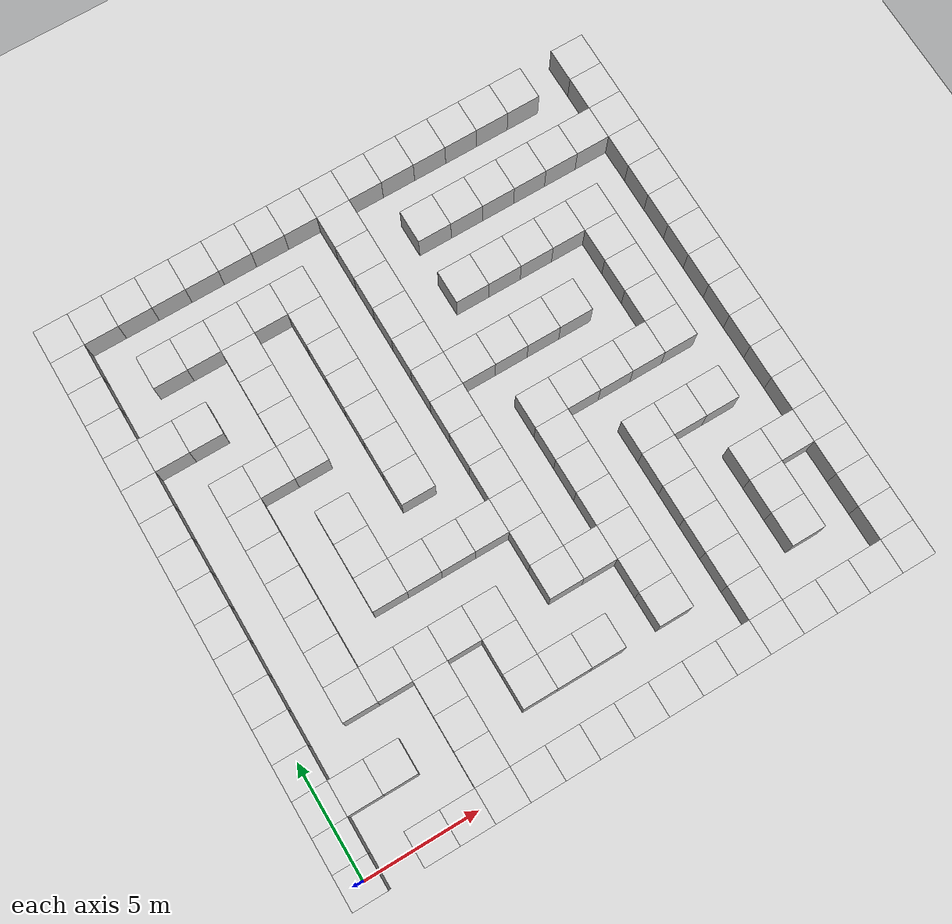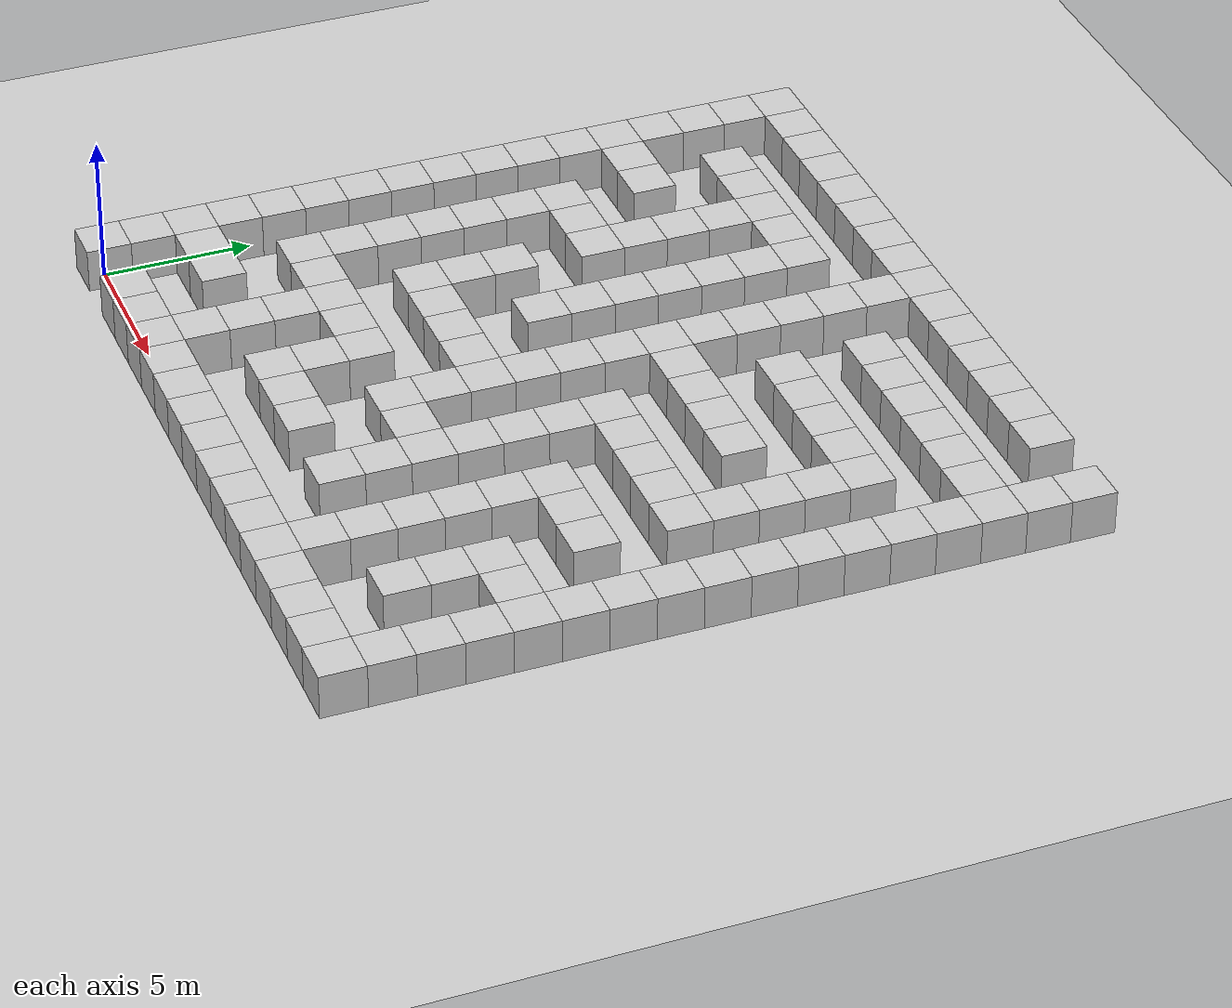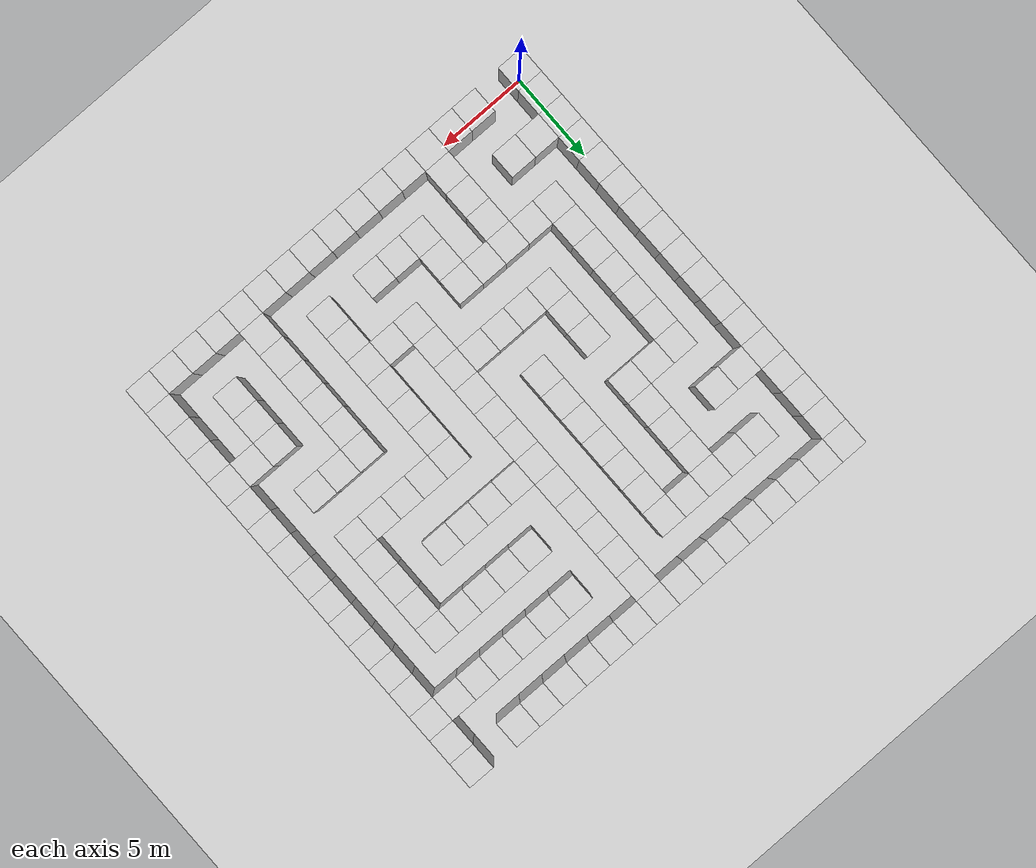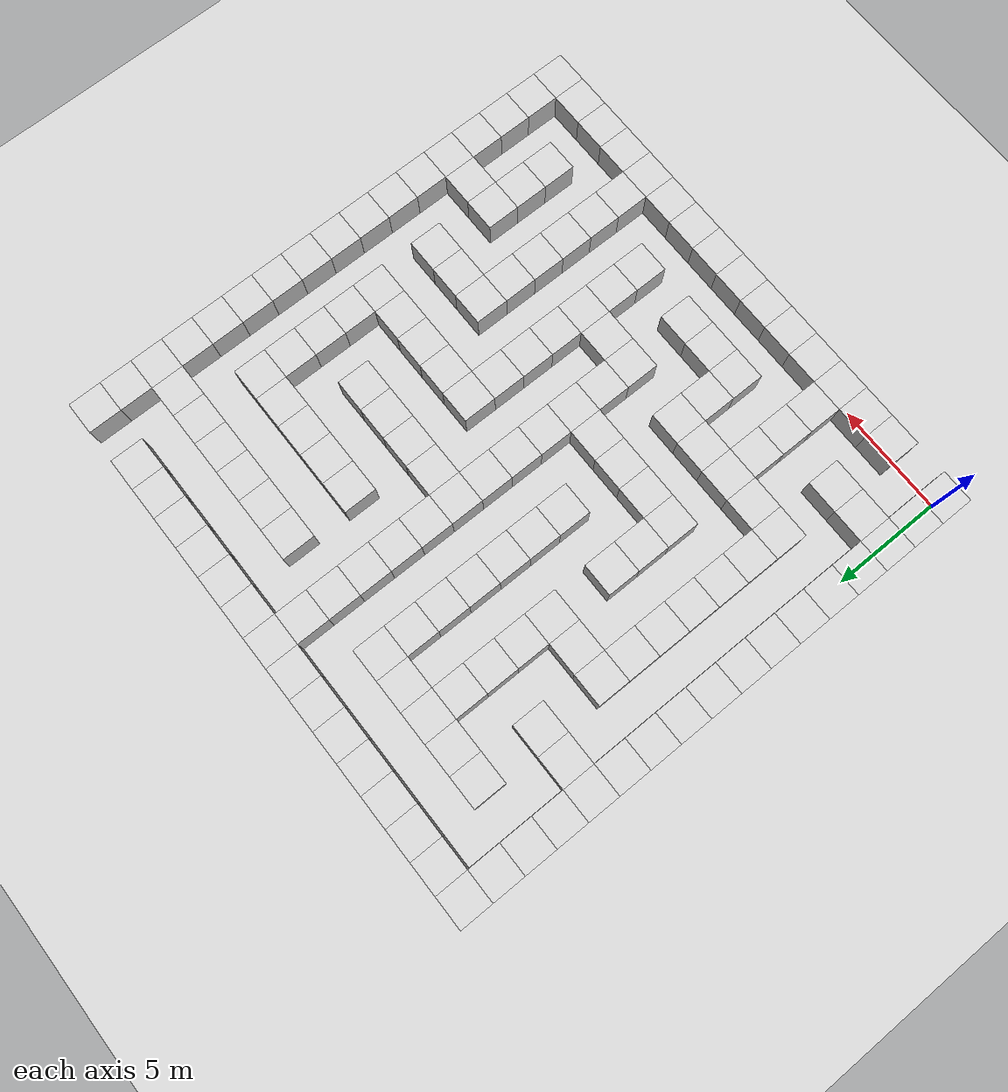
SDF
<?xml version="1.0"?>
<sdf version="1.9">
  <world name="maze_world">
    <physics name="1ms" type="ignored">
      <max_step_size>0.001</max_step_size>
      <real_time_factor>1.0</real_time_factor>
    </physics>
    <plugin filename="gz-sim-physics-system" name="gz::sim::systems::Physics"/>
    <plugin filename="gz-sim-scene-broadcaster-system" name="gz::sim::systems::SceneBroadcaster"/>
    <plugin filename="gz-sim-user-commands-system" name="gz::sim::systems::UserCommands"/>

    <include><uri>https://fuel.gazebosim.org/1.0/OpenRobotics/models/Sun</uri></include>
    <include><uri>https://fuel.gazebosim.org/1.0/OpenRobotics/models/Ground Plane</uri></include>
    <model name='wall_0_0'>
      <static>true</static>
      <pose>0 0 0.75 0 0 0</pose>
      <link name='link'>
        <collision name='collision'><geometry><box><size>1.5 1.5 1.5</size></box></geometry></collision>
        <visual name='visual'><geometry><box><size>1.5 1.5 1.5</size></box></geometry>
          <material>
            <ambient>0.8 0.8 0.8 1</ambient>
            <diffuse>0.8 0.8 0.8 1</diffuse>
            <pbr>
              <metal>
                <albedo_map>file:///home/max/Repos/DHBW-Robotik/maze_runner_ws/src/maze_runner_gazebo/textures/simple_box.png</albedo_map>
                <roughness>0.9</roughness>
              </metal>
            </pbr>
          </material>
        </visual>
      </link>
    </model>
    <model name='wall_2_0'>
      <static>true</static>
      <pose>3 0 0.75 0 0 0</pose>
      <link name='link'>
        <collision name='collision'><geometry><box><size>1.5 1.5 1.5</size></box></geometry></collision>
        <visual name='visual'><geometry><box><size>1.5 1.5 1.5</size></box></geometry>
          <material>
            <ambient>0.8 0.8 0.8 1</ambient>
            <diffuse>0.8 0.8 0.8 1</diffuse>
            <pbr>
              <metal>
                <albedo_map>file:///home/max/Repos/DHBW-Robotik/maze_runner_ws/src/maze_runner_gazebo/textures/simple_box.png</albedo_map>
                <roughness>0.9</roughness>
              </metal>
            </pbr>
          </material>
        </visual>
      </link>
    </model>
    <model name='wall_3_0'>
      <static>true</static>
      <pose>4.5 0 0.75 0 0 0</pose>
      <link name='link'>
        <collision name='collision'><geometry><box><size>1.5 1.5 1.5</size></box></geometry></collision>
        <visual name='visual'><geometry><box><size>1.5 1.5 1.5</size></box></geometry>
          <material>
            <ambient>0.8 0.8 0.8 1</ambient>
            <diffuse>0.8 0.8 0.8 1</diffuse>
            <pbr>
              <metal>
                <albedo_map>file:///home/max/Repos/DHBW-Robotik/maze_runner_ws/src/maze_runner_gazebo/textures/simple_box.png</albedo_map>
                <roughness>0.9</roughness>
              </metal>
            </pbr>
          </material>
        </visual>
      </link>
    </model>
    <model name='wall_4_0'>
      <static>true</static>
      <pose>6 0 0.75 0 0 0</pose>
      <link name='link'>
        <collision name='collision'><geometry><box><size>1.5 1.5 1.5</size></box></geometry></collision>
        <visual name='visual'><geometry><box><size>1.5 1.5 1.5</size></box></geometry>
          <material>
            <ambient>0.8 0.8 0.8 1</ambient>
            <diffuse>0.8 0.8 0.8 1</diffuse>
            <pbr>
              <metal>
                <albedo_map>file:///home/max/Repos/DHBW-Robotik/maze_runner_ws/src/maze_runner_gazebo/textures/simple_box.png</albedo_map>
                <roughness>0.9</roughness>
              </metal>
            </pbr>
          </material>
        </visual>
      </link>
    </model>
    <model name='wall_5_0'>
      <static>true</static>
      <pose>7.5 0 0.75 0 0 0</pose>
      <link name='link'>
        <collision name='collision'><geometry><box><size>1.5 1.5 1.5</size></box></geometry></collision>
        <visual name='visual'><geometry><box><size>1.5 1.5 1.5</size></box></geometry>
          <material>
            <ambient>0.8 0.8 0.8 1</ambient>
            <diffuse>0.8 0.8 0.8 1</diffuse>
            <pbr>
              <metal>
                <albedo_map>file:///home/max/Repos/DHBW-Robotik/maze_runner_ws/src/maze_runner_gazebo/textures/simple_box.png</albedo_map>
                <roughness>0.9</roughness>
              </metal>
            </pbr>
          </material>
        </visual>
      </link>
    </model>
    <model name='wall_6_0'>
      <static>true</static>
      <pose>9 0 0.75 0 0 0</pose>
      <link name='link'>
        <collision name='collision'><geometry><box><size>1.5 1.5 1.5</size></box></geometry></collision>
        <visual name='visual'><geometry><box><size>1.5 1.5 1.5</size></box></geometry>
          <material>
            <ambient>0.8 0.8 0.8 1</ambient>
            <diffuse>0.8 0.8 0.8 1</diffuse>
            <pbr>
              <metal>
                <albedo_map>file:///home/max/Repos/DHBW-Robotik/maze_runner_ws/src/maze_runner_gazebo/textures/simple_box.png</albedo_map>
                <roughness>0.9</roughness>
              </metal>
            </pbr>
          </material>
        </visual>
      </link>
    </model>
    <model name='wall_7_0'>
      <static>true</static>
      <pose>10.5 0 0.75 0 0 0</pose>
      <link name='link'>
        <collision name='collision'><geometry><box><size>1.5 1.5 1.5</size></box></geometry></collision>
        <visual name='visual'><geometry><box><size>1.5 1.5 1.5</size></box></geometry>
          <material>
            <ambient>0.8 0.8 0.8 1</ambient>
            <diffuse>0.8 0.8 0.8 1</diffuse>
            <pbr>
              <metal>
                <albedo_map>file:///home/max/Repos/DHBW-Robotik/maze_runner_ws/src/maze_runner_gazebo/textures/simple_box.png</albedo_map>
                <roughness>0.9</roughness>
              </metal>
            </pbr>
          </material>
        </visual>
      </link>
    </model>
    <model name='wall_8_0'>
      <static>true</static>
      <pose>12 0 0.75 0 0 0</pose>
      <link name='link'>
        <collision name='collision'><geometry><box><size>1.5 1.5 1.5</size></box></geometry></collision>
        <visual name='visual'><geometry><box><size>1.5 1.5 1.5</size></box></geometry>
          <material>
            <ambient>0.8 0.8 0.8 1</ambient>
            <diffuse>0.8 0.8 0.8 1</diffuse>
            <pbr>
              <metal>
                <albedo_map>file:///home/max/Repos/DHBW-Robotik/maze_runner_ws/src/maze_runner_gazebo/textures/simple_box.png</albedo_map>
                <roughness>0.9</roughness>
              </metal>
            </pbr>
          </material>
        </visual>
      </link>
    </model>
    <model name='wall_9_0'>
      <static>true</static>
      <pose>13.5 0 0.75 0 0 0</pose>
      <link name='link'>
        <collision name='collision'><geometry><box><size>1.5 1.5 1.5</size></box></geometry></collision>
        <visual name='visual'><geometry><box><size>1.5 1.5 1.5</size></box></geometry>
          <material>
            <ambient>0.8 0.8 0.8 1</ambient>
            <diffuse>0.8 0.8 0.8 1</diffuse>
            <pbr>
              <metal>
                <albedo_map>file:///home/max/Repos/DHBW-Robotik/maze_runner_ws/src/maze_runner_gazebo/textures/simple_box.png</albedo_map>
                <roughness>0.9</roughness>
              </metal>
            </pbr>
          </material>
        </visual>
      </link>
    </model>
    <model name='wall_10_0'>
      <static>true</static>
      <pose>15 0 0.75 0 0 0</pose>
      <link name='link'>
        <collision name='collision'><geometry><box><size>1.5 1.5 1.5</size></box></geometry></collision>
        <visual name='visual'><geometry><box><size>1.5 1.5 1.5</size></box></geometry>
          <material>
            <ambient>0.8 0.8 0.8 1</ambient>
            <diffuse>0.8 0.8 0.8 1</diffuse>
            <pbr>
              <metal>
                <albedo_map>file:///home/max/Repos/DHBW-Robotik/maze_runner_ws/src/maze_runner_gazebo/textures/simple_box.png</albedo_map>
                <roughness>0.9</roughness>
              </metal>
            </pbr>
          </material>
        </visual>
      </link>
    </model>
    <model name='wall_11_0'>
      <static>true</static>
      <pose>16.5 0 0.75 0 0 0</pose>
      <link name='link'>
        <collision name='collision'><geometry><box><size>1.5 1.5 1.5</size></box></geometry></collision>
        <visual name='visual'><geometry><box><size>1.5 1.5 1.5</size></box></geometry>
          <material>
            <ambient>0.8 0.8 0.8 1</ambient>
            <diffuse>0.8 0.8 0.8 1</diffuse>
            <pbr>
              <metal>
                <albedo_map>file:///home/max/Repos/DHBW-Robotik/maze_runner_ws/src/maze_runner_gazebo/textures/simple_box.png</albedo_map>
                <roughness>0.9</roughness>
              </metal>
            </pbr>
          </material>
        </visual>
      </link>
    </model>
    <model name='wall_12_0'>
      <static>true</static>
      <pose>18 0 0.75 0 0 0</pose>
      <link name='link'>
        <collision name='collision'><geometry><box><size>1.5 1.5 1.5</size></box></geometry></collision>
        <visual name='visual'><geometry><box><size>1.5 1.5 1.5</size></box></geometry>
          <material>
            <ambient>0.8 0.8 0.8 1</ambient>
            <diffuse>0.8 0.8 0.8 1</diffuse>
            <pbr>
              <metal>
                <albedo_map>file:///home/max/Repos/DHBW-Robotik/maze_runner_ws/src/maze_runner_gazebo/textures/simple_box.png</albedo_map>
                <roughness>0.9</roughness>
              </metal>
            </pbr>
          </material>
        </visual>
      </link>
    </model>
    <model name='wall_13_0'>
      <static>true</static>
      <pose>19.5 0 0.75 0 0 0</pose>
      <link name='link'>
        <collision name='collision'><geometry><box><size>1.5 1.5 1.5</size></box></geometry></collision>
        <visual name='visual'><geometry><box><size>1.5 1.5 1.5</size></box></geometry>
          <material>
            <ambient>0.8 0.8 0.8 1</ambient>
            <diffuse>0.8 0.8 0.8 1</diffuse>
            <pbr>
              <metal>
                <albedo_map>file:///home/max/Repos/DHBW-Robotik/maze_runner_ws/src/maze_runner_gazebo/textures/simple_box.png</albedo_map>
                <roughness>0.9</roughness>
              </metal>
            </pbr>
          </material>
        </visual>
      </link>
    </model>
    <model name='wall_14_0'>
      <static>true</static>
      <pose>21 0 0.75 0 0 0</pose>
      <link name='link'>
        <collision name='collision'><geometry><box><size>1.5 1.5 1.5</size></box></geometry></collision>
        <visual name='visual'><geometry><box><size>1.5 1.5 1.5</size></box></geometry>
          <material>
            <ambient>0.8 0.8 0.8 1</ambient>
            <diffuse>0.8 0.8 0.8 1</diffuse>
            <pbr>
              <metal>
                <albedo_map>file:///home/max/Repos/DHBW-Robotik/maze_runner_ws/src/maze_runner_gazebo/textures/simple_box.png</albedo_map>
                <roughness>0.9</roughness>
              </metal>
            </pbr>
          </material>
        </visual>
      </link>
    </model>
    <model name='wall_15_0'>
      <static>true</static>
      <pose>22.5 0 0.75 0 0 0</pose>
      <link name='link'>
        <collision name='collision'><geometry><box><size>1.5 1.5 1.5</size></box></geometry></collision>
        <visual name='visual'><geometry><box><size>1.5 1.5 1.5</size></box></geometry>
          <material>
            <ambient>0.8 0.8 0.8 1</ambient>
            <diffuse>0.8 0.8 0.8 1</diffuse>
            <pbr>
              <metal>
                <albedo_map>file:///home/max/Repos/DHBW-Robotik/maze_runner_ws/src/maze_runner_gazebo/textures/simple_box.png</albedo_map>
                <roughness>0.9</roughness>
              </metal>
            </pbr>
          </material>
        </visual>
      </link>
    </model>
    <model name='wall_16_0'>
      <static>true</static>
      <pose>24 0 0.75 0 0 0</pose>
      <link name='link'>
        <collision name='collision'><geometry><box><size>1.5 1.5 1.5</size></box></geometry></collision>
        <visual name='visual'><geometry><box><size>1.5 1.5 1.5</size></box></geometry>
          <material>
            <ambient>0.8 0.8 0.8 1</ambient>
            <diffuse>0.8 0.8 0.8 1</diffuse>
            <pbr>
              <metal>
                <albedo_map>file:///home/max/Repos/DHBW-Robotik/maze_runner_ws/src/maze_runner_gazebo/textures/simple_box.png</albedo_map>
                <roughness>0.9</roughness>
              </metal>
            </pbr>
          </material>
        </visual>
      </link>
    </model>
    <model name='wall_0_1'>
      <static>true</static>
      <pose>0 1.5 0.75 0 0 0</pose>
      <link name='link'>
        <collision name='collision'><geometry><box><size>1.5 1.5 1.5</size></box></geometry></collision>
        <visual name='visual'><geometry><box><size>1.5 1.5 1.5</size></box></geometry>
          <material>
            <ambient>0.8 0.8 0.8 1</ambient>
            <diffuse>0.8 0.8 0.8 1</diffuse>
            <pbr>
              <metal>
                <albedo_map>file:///home/max/Repos/DHBW-Robotik/maze_runner_ws/src/maze_runner_gazebo/textures/simple_box.png</albedo_map>
                <roughness>0.9</roughness>
              </metal>
            </pbr>
          </material>
        </visual>
      </link>
    </model>
    <model name='wall_4_1'>
      <static>true</static>
      <pose>6 1.5 0.75 0 0 0</pose>
      <link name='link'>
        <collision name='collision'><geometry><box><size>1.5 1.5 1.5</size></box></geometry></collision>
        <visual name='visual'><geometry><box><size>1.5 1.5 1.5</size></box></geometry>
          <material>
            <ambient>0.8 0.8 0.8 1</ambient>
            <diffuse>0.8 0.8 0.8 1</diffuse>
            <pbr>
              <metal>
                <albedo_map>file:///home/max/Repos/DHBW-Robotik/maze_runner_ws/src/maze_runner_gazebo/textures/simple_box.png</albedo_map>
                <roughness>0.9</roughness>
              </metal>
            </pbr>
          </material>
        </visual>
      </link>
    </model>
    <model name='wall_12_1'>
      <static>true</static>
      <pose>18 1.5 0.75 0 0 0</pose>
      <link name='link'>
        <collision name='collision'><geometry><box><size>1.5 1.5 1.5</size></box></geometry></collision>
        <visual name='visual'><geometry><box><size>1.5 1.5 1.5</size></box></geometry>
          <material>
            <ambient>0.8 0.8 0.8 1</ambient>
            <diffuse>0.8 0.8 0.8 1</diffuse>
            <pbr>
              <metal>
                <albedo_map>file:///home/max/Repos/DHBW-Robotik/maze_runner_ws/src/maze_runner_gazebo/textures/simple_box.png</albedo_map>
                <roughness>0.9</roughness>
              </metal>
            </pbr>
          </material>
        </visual>
      </link>
    </model>
    <model name='wall_16_1'>
      <static>true</static>
      <pose>24 1.5 0.75 0 0 0</pose>
      <link name='link'>
        <collision name='collision'><geometry><box><size>1.5 1.5 1.5</size></box></geometry></collision>
        <visual name='visual'><geometry><box><size>1.5 1.5 1.5</size></box></geometry>
          <material>
            <ambient>0.8 0.8 0.8 1</ambient>
            <diffuse>0.8 0.8 0.8 1</diffuse>
            <pbr>
              <metal>
                <albedo_map>file:///home/max/Repos/DHBW-Robotik/maze_runner_ws/src/maze_runner_gazebo/textures/simple_box.png</albedo_map>
                <roughness>0.9</roughness>
              </metal>
            </pbr>
          </material>
        </visual>
      </link>
    </model>
    <model name='wall_0_2'>
      <static>true</static>
      <pose>0 3 0.75 0 0 0</pose>
      <link name='link'>
        <collision name='collision'><geometry><box><size>1.5 1.5 1.5</size></box></geometry></collision>
        <visual name='visual'><geometry><box><size>1.5 1.5 1.5</size></box></geometry>
          <material>
            <ambient>0.8 0.8 0.8 1</ambient>
            <diffuse>0.8 0.8 0.8 1</diffuse>
            <pbr>
              <metal>
                <albedo_map>file:///home/max/Repos/DHBW-Robotik/maze_runner_ws/src/maze_runner_gazebo/textures/simple_box.png</albedo_map>
                <roughness>0.9</roughness>
              </metal>
            </pbr>
          </material>
        </visual>
      </link>
    </model>
    <model name='wall_1_2'>
      <static>true</static>
      <pose>1.5 3 0.75 0 0 0</pose>
      <link name='link'>
        <collision name='collision'><geometry><box><size>1.5 1.5 1.5</size></box></geometry></collision>
        <visual name='visual'><geometry><box><size>1.5 1.5 1.5</size></box></geometry>
          <material>
            <ambient>0.8 0.8 0.8 1</ambient>
            <diffuse>0.8 0.8 0.8 1</diffuse>
            <pbr>
              <metal>
                <albedo_map>file:///home/max/Repos/DHBW-Robotik/maze_runner_ws/src/maze_runner_gazebo/textures/simple_box.png</albedo_map>
                <roughness>0.9</roughness>
              </metal>
            </pbr>
          </material>
        </visual>
      </link>
    </model>
    <model name='wall_2_2'>
      <static>true</static>
      <pose>3 3 0.75 0 0 0</pose>
      <link name='link'>
        <collision name='collision'><geometry><box><size>1.5 1.5 1.5</size></box></geometry></collision>
        <visual name='visual'><geometry><box><size>1.5 1.5 1.5</size></box></geometry>
          <material>
            <ambient>0.8 0.8 0.8 1</ambient>
            <diffuse>0.8 0.8 0.8 1</diffuse>
            <pbr>
              <metal>
                <albedo_map>file:///home/max/Repos/DHBW-Robotik/maze_runner_ws/src/maze_runner_gazebo/textures/simple_box.png</albedo_map>
                <roughness>0.9</roughness>
              </metal>
            </pbr>
          </material>
        </visual>
      </link>
    </model>
    <model name='wall_4_2'>
      <static>true</static>
      <pose>6 3 0.75 0 0 0</pose>
      <link name='link'>
        <collision name='collision'><geometry><box><size>1.5 1.5 1.5</size></box></geometry></collision>
        <visual name='visual'><geometry><box><size>1.5 1.5 1.5</size></box></geometry>
          <material>
            <ambient>0.8 0.8 0.8 1</ambient>
            <diffuse>0.8 0.8 0.8 1</diffuse>
            <pbr>
              <metal>
                <albedo_map>file:///home/max/Repos/DHBW-Robotik/maze_runner_ws/src/maze_runner_gazebo/textures/simple_box.png</albedo_map>
                <roughness>0.9</roughness>
              </metal>
            </pbr>
          </material>
        </visual>
      </link>
    </model>
    <model name='wall_6_2'>
      <static>true</static>
      <pose>9 3 0.75 0 0 0</pose>
      <link name='link'>
        <collision name='collision'><geometry><box><size>1.5 1.5 1.5</size></box></geometry></collision>
        <visual name='visual'><geometry><box><size>1.5 1.5 1.5</size></box></geometry>
          <material>
            <ambient>0.8 0.8 0.8 1</ambient>
            <diffuse>0.8 0.8 0.8 1</diffuse>
            <pbr>
              <metal>
                <albedo_map>file:///home/max/Repos/DHBW-Robotik/maze_runner_ws/src/maze_runner_gazebo/textures/simple_box.png</albedo_map>
                <roughness>0.9</roughness>
              </metal>
            </pbr>
          </material>
        </visual>
      </link>
    </model>
    <model name='wall_7_2'>
      <static>true</static>
      <pose>10.5 3 0.75 0 0 0</pose>
      <link name='link'>
        <collision name='collision'><geometry><box><size>1.5 1.5 1.5</size></box></geometry></collision>
        <visual name='visual'><geometry><box><size>1.5 1.5 1.5</size></box></geometry>
          <material>
            <ambient>0.8 0.8 0.8 1</ambient>
            <diffuse>0.8 0.8 0.8 1</diffuse>
            <pbr>
              <metal>
                <albedo_map>file:///home/max/Repos/DHBW-Robotik/maze_runner_ws/src/maze_runner_gazebo/textures/simple_box.png</albedo_map>
                <roughness>0.9</roughness>
              </metal>
            </pbr>
          </material>
        </visual>
      </link>
    </model>
    <model name='wall_8_2'>
      <static>true</static>
      <pose>12 3 0.75 0 0 0</pose>
      <link name='link'>
        <collision name='collision'><geometry><box><size>1.5 1.5 1.5</size></box></geometry></collision>
        <visual name='visual'><geometry><box><size>1.5 1.5 1.5</size></box></geometry>
          <material>
            <ambient>0.8 0.8 0.8 1</ambient>
            <diffuse>0.8 0.8 0.8 1</diffuse>
            <pbr>
              <metal>
                <albedo_map>file:///home/max/Repos/DHBW-Robotik/maze_runner_ws/src/maze_runner_gazebo/textures/simple_box.png</albedo_map>
                <roughness>0.9</roughness>
              </metal>
            </pbr>
          </material>
        </visual>
      </link>
    </model>
    <model name='wall_10_2'>
      <static>true</static>
      <pose>15 3 0.75 0 0 0</pose>
      <link name='link'>
        <collision name='collision'><geometry><box><size>1.5 1.5 1.5</size></box></geometry></collision>
        <visual name='visual'><geometry><box><size>1.5 1.5 1.5</size></box></geometry>
          <material>
            <ambient>0.8 0.8 0.8 1</ambient>
            <diffuse>0.8 0.8 0.8 1</diffuse>
            <pbr>
              <metal>
                <albedo_map>file:///home/max/Repos/DHBW-Robotik/maze_runner_ws/src/maze_runner_gazebo/textures/simple_box.png</albedo_map>
                <roughness>0.9</roughness>
              </metal>
            </pbr>
          </material>
        </visual>
      </link>
    </model>
    <model name='wall_12_2'>
      <static>true</static>
      <pose>18 3 0.75 0 0 0</pose>
      <link name='link'>
        <collision name='collision'><geometry><box><size>1.5 1.5 1.5</size></box></geometry></collision>
        <visual name='visual'><geometry><box><size>1.5 1.5 1.5</size></box></geometry>
          <material>
            <ambient>0.8 0.8 0.8 1</ambient>
            <diffuse>0.8 0.8 0.8 1</diffuse>
            <pbr>
              <metal>
                <albedo_map>file:///home/max/Repos/DHBW-Robotik/maze_runner_ws/src/maze_runner_gazebo/textures/simple_box.png</albedo_map>
                <roughness>0.9</roughness>
              </metal>
            </pbr>
          </material>
        </visual>
      </link>
    </model>
    <model name='wall_14_2'>
      <static>true</static>
      <pose>21 3 0.75 0 0 0</pose>
      <link name='link'>
        <collision name='collision'><geometry><box><size>1.5 1.5 1.5</size></box></geometry></collision>
        <visual name='visual'><geometry><box><size>1.5 1.5 1.5</size></box></geometry>
          <material>
            <ambient>0.8 0.8 0.8 1</ambient>
            <diffuse>0.8 0.8 0.8 1</diffuse>
            <pbr>
              <metal>
                <albedo_map>file:///home/max/Repos/DHBW-Robotik/maze_runner_ws/src/maze_runner_gazebo/textures/simple_box.png</albedo_map>
                <roughness>0.9</roughness>
              </metal>
            </pbr>
          </material>
        </visual>
      </link>
    </model>
    <model name='wall_16_2'>
      <static>true</static>
      <pose>24 3 0.75 0 0 0</pose>
      <link name='link'>
        <collision name='collision'><geometry><box><size>1.5 1.5 1.5</size></box></geometry></collision>
        <visual name='visual'><geometry><box><size>1.5 1.5 1.5</size></box></geometry>
          <material>
            <ambient>0.8 0.8 0.8 1</ambient>
            <diffuse>0.8 0.8 0.8 1</diffuse>
            <pbr>
              <metal>
                <albedo_map>file:///home/max/Repos/DHBW-Robotik/maze_runner_ws/src/maze_runner_gazebo/textures/simple_box.png</albedo_map>
                <roughness>0.9</roughness>
              </metal>
            </pbr>
          </material>
        </visual>
      </link>
    </model>
    <model name='wall_0_3'>
      <static>true</static>
      <pose>0 4.5 0.75 0 0 0</pose>
      <link name='link'>
        <collision name='collision'><geometry><box><size>1.5 1.5 1.5</size></box></geometry></collision>
        <visual name='visual'><geometry><box><size>1.5 1.5 1.5</size></box></geometry>
          <material>
            <ambient>0.8 0.8 0.8 1</ambient>
            <diffuse>0.8 0.8 0.8 1</diffuse>
            <pbr>
              <metal>
                <albedo_map>file:///home/max/Repos/DHBW-Robotik/maze_runner_ws/src/maze_runner_gazebo/textures/simple_box.png</albedo_map>
                <roughness>0.9</roughness>
              </metal>
            </pbr>
          </material>
        </visual>
      </link>
    </model>
    <model name='wall_4_3'>
      <static>true</static>
      <pose>6 4.5 0.75 0 0 0</pose>
      <link name='link'>
        <collision name='collision'><geometry><box><size>1.5 1.5 1.5</size></box></geometry></collision>
        <visual name='visual'><geometry><box><size>1.5 1.5 1.5</size></box></geometry>
          <material>
            <ambient>0.8 0.8 0.8 1</ambient>
            <diffuse>0.8 0.8 0.8 1</diffuse>
            <pbr>
              <metal>
                <albedo_map>file:///home/max/Repos/DHBW-Robotik/maze_runner_ws/src/maze_runner_gazebo/textures/simple_box.png</albedo_map>
                <roughness>0.9</roughness>
              </metal>
            </pbr>
          </material>
        </visual>
      </link>
    </model>
    <model name='wall_6_3'>
      <static>true</static>
      <pose>9 4.5 0.75 0 0 0</pose>
      <link name='link'>
        <collision name='collision'><geometry><box><size>1.5 1.5 1.5</size></box></geometry></collision>
        <visual name='visual'><geometry><box><size>1.5 1.5 1.5</size></box></geometry>
          <material>
            <ambient>0.8 0.8 0.8 1</ambient>
            <diffuse>0.8 0.8 0.8 1</diffuse>
            <pbr>
              <metal>
                <albedo_map>file:///home/max/Repos/DHBW-Robotik/maze_runner_ws/src/maze_runner_gazebo/textures/simple_box.png</albedo_map>
                <roughness>0.9</roughness>
              </metal>
            </pbr>
          </material>
        </visual>
      </link>
    </model>
    <model name='wall_10_3'>
      <static>true</static>
      <pose>15 4.5 0.75 0 0 0</pose>
      <link name='link'>
        <collision name='collision'><geometry><box><size>1.5 1.5 1.5</size></box></geometry></collision>
        <visual name='visual'><geometry><box><size>1.5 1.5 1.5</size></box></geometry>
          <material>
            <ambient>0.8 0.8 0.8 1</ambient>
            <diffuse>0.8 0.8 0.8 1</diffuse>
            <pbr>
              <metal>
                <albedo_map>file:///home/max/Repos/DHBW-Robotik/maze_runner_ws/src/maze_runner_gazebo/textures/simple_box.png</albedo_map>
                <roughness>0.9</roughness>
              </metal>
            </pbr>
          </material>
        </visual>
      </link>
    </model>
    <model name='wall_12_3'>
      <static>true</static>
      <pose>18 4.5 0.75 0 0 0</pose>
      <link name='link'>
        <collision name='collision'><geometry><box><size>1.5 1.5 1.5</size></box></geometry></collision>
        <visual name='visual'><geometry><box><size>1.5 1.5 1.5</size></box></geometry>
          <material>
            <ambient>0.8 0.8 0.8 1</ambient>
            <diffuse>0.8 0.8 0.8 1</diffuse>
            <pbr>
              <metal>
                <albedo_map>file:///home/max/Repos/DHBW-Robotik/maze_runner_ws/src/maze_runner_gazebo/textures/simple_box.png</albedo_map>
                <roughness>0.9</roughness>
              </metal>
            </pbr>
          </material>
        </visual>
      </link>
    </model>
    <model name='wall_14_3'>
      <static>true</static>
      <pose>21 4.5 0.75 0 0 0</pose>
      <link name='link'>
        <collision name='collision'><geometry><box><size>1.5 1.5 1.5</size></box></geometry></collision>
        <visual name='visual'><geometry><box><size>1.5 1.5 1.5</size></box></geometry>
          <material>
            <ambient>0.8 0.8 0.8 1</ambient>
            <diffuse>0.8 0.8 0.8 1</diffuse>
            <pbr>
              <metal>
                <albedo_map>file:///home/max/Repos/DHBW-Robotik/maze_runner_ws/src/maze_runner_gazebo/textures/simple_box.png</albedo_map>
                <roughness>0.9</roughness>
              </metal>
            </pbr>
          </material>
        </visual>
      </link>
    </model>
    <model name='wall_16_3'>
      <static>true</static>
      <pose>24 4.5 0.75 0 0 0</pose>
      <link name='link'>
        <collision name='collision'><geometry><box><size>1.5 1.5 1.5</size></box></geometry></collision>
        <visual name='visual'><geometry><box><size>1.5 1.5 1.5</size></box></geometry>
          <material>
            <ambient>0.8 0.8 0.8 1</ambient>
            <diffuse>0.8 0.8 0.8 1</diffuse>
            <pbr>
              <metal>
                <albedo_map>file:///home/max/Repos/DHBW-Robotik/maze_runner_ws/src/maze_runner_gazebo/textures/simple_box.png</albedo_map>
                <roughness>0.9</roughness>
              </metal>
            </pbr>
          </material>
        </visual>
      </link>
    </model>
    <model name='wall_0_4'>
      <static>true</static>
      <pose>0 6 0.75 0 0 0</pose>
      <link name='link'>
        <collision name='collision'><geometry><box><size>1.5 1.5 1.5</size></box></geometry></collision>
        <visual name='visual'><geometry><box><size>1.5 1.5 1.5</size></box></geometry>
          <material>
            <ambient>0.8 0.8 0.8 1</ambient>
            <diffuse>0.8 0.8 0.8 1</diffuse>
            <pbr>
              <metal>
                <albedo_map>file:///home/max/Repos/DHBW-Robotik/maze_runner_ws/src/maze_runner_gazebo/textures/simple_box.png</albedo_map>
                <roughness>0.9</roughness>
              </metal>
            </pbr>
          </material>
        </visual>
      </link>
    </model>
    <model name='wall_2_4'>
      <static>true</static>
      <pose>3 6 0.75 0 0 0</pose>
      <link name='link'>
        <collision name='collision'><geometry><box><size>1.5 1.5 1.5</size></box></geometry></collision>
        <visual name='visual'><geometry><box><size>1.5 1.5 1.5</size></box></geometry>
          <material>
            <ambient>0.8 0.8 0.8 1</ambient>
            <diffuse>0.8 0.8 0.8 1</diffuse>
            <pbr>
              <metal>
                <albedo_map>file:///home/max/Repos/DHBW-Robotik/maze_runner_ws/src/maze_runner_gazebo/textures/simple_box.png</albedo_map>
                <roughness>0.9</roughness>
              </metal>
            </pbr>
          </material>
        </visual>
      </link>
    </model>
    <model name='wall_3_4'>
      <static>true</static>
      <pose>4.5 6 0.75 0 0 0</pose>
      <link name='link'>
        <collision name='collision'><geometry><box><size>1.5 1.5 1.5</size></box></geometry></collision>
        <visual name='visual'><geometry><box><size>1.5 1.5 1.5</size></box></geometry>
          <material>
            <ambient>0.8 0.8 0.8 1</ambient>
            <diffuse>0.8 0.8 0.8 1</diffuse>
            <pbr>
              <metal>
                <albedo_map>file:///home/max/Repos/DHBW-Robotik/maze_runner_ws/src/maze_runner_gazebo/textures/simple_box.png</albedo_map>
                <roughness>0.9</roughness>
              </metal>
            </pbr>
          </material>
        </visual>
      </link>
    </model>
    <model name='wall_4_4'>
      <static>true</static>
      <pose>6 6 0.75 0 0 0</pose>
      <link name='link'>
        <collision name='collision'><geometry><box><size>1.5 1.5 1.5</size></box></geometry></collision>
        <visual name='visual'><geometry><box><size>1.5 1.5 1.5</size></box></geometry>
          <material>
            <ambient>0.8 0.8 0.8 1</ambient>
            <diffuse>0.8 0.8 0.8 1</diffuse>
            <pbr>
              <metal>
                <albedo_map>file:///home/max/Repos/DHBW-Robotik/maze_runner_ws/src/maze_runner_gazebo/textures/simple_box.png</albedo_map>
                <roughness>0.9</roughness>
              </metal>
            </pbr>
          </material>
        </visual>
      </link>
    </model>
    <model name='wall_5_4'>
      <static>true</static>
      <pose>7.5 6 0.75 0 0 0</pose>
      <link name='link'>
        <collision name='collision'><geometry><box><size>1.5 1.5 1.5</size></box></geometry></collision>
        <visual name='visual'><geometry><box><size>1.5 1.5 1.5</size></box></geometry>
          <material>
            <ambient>0.8 0.8 0.8 1</ambient>
            <diffuse>0.8 0.8 0.8 1</diffuse>
            <pbr>
              <metal>
                <albedo_map>file:///home/max/Repos/DHBW-Robotik/maze_runner_ws/src/maze_runner_gazebo/textures/simple_box.png</albedo_map>
                <roughness>0.9</roughness>
              </metal>
            </pbr>
          </material>
        </visual>
      </link>
    </model>
    <model name='wall_6_4'>
      <static>true</static>
      <pose>9 6 0.75 0 0 0</pose>
      <link name='link'>
        <collision name='collision'><geometry><box><size>1.5 1.5 1.5</size></box></geometry></collision>
        <visual name='visual'><geometry><box><size>1.5 1.5 1.5</size></box></geometry>
          <material>
            <ambient>0.8 0.8 0.8 1</ambient>
            <diffuse>0.8 0.8 0.8 1</diffuse>
            <pbr>
              <metal>
                <albedo_map>file:///home/max/Repos/DHBW-Robotik/maze_runner_ws/src/maze_runner_gazebo/textures/simple_box.png</albedo_map>
                <roughness>0.9</roughness>
              </metal>
            </pbr>
          </material>
        </visual>
      </link>
    </model>
    <model name='wall_8_4'>
      <static>true</static>
      <pose>12 6 0.75 0 0 0</pose>
      <link name='link'>
        <collision name='collision'><geometry><box><size>1.5 1.5 1.5</size></box></geometry></collision>
        <visual name='visual'><geometry><box><size>1.5 1.5 1.5</size></box></geometry>
          <material>
            <ambient>0.8 0.8 0.8 1</ambient>
            <diffuse>0.8 0.8 0.8 1</diffuse>
            <pbr>
              <metal>
                <albedo_map>file:///home/max/Repos/DHBW-Robotik/maze_runner_ws/src/maze_runner_gazebo/textures/simple_box.png</albedo_map>
                <roughness>0.9</roughness>
              </metal>
            </pbr>
          </material>
        </visual>
      </link>
    </model>
    <model name='wall_9_4'>
      <static>true</static>
      <pose>13.5 6 0.75 0 0 0</pose>
      <link name='link'>
        <collision name='collision'><geometry><box><size>1.5 1.5 1.5</size></box></geometry></collision>
        <visual name='visual'><geometry><box><size>1.5 1.5 1.5</size></box></geometry>
          <material>
            <ambient>0.8 0.8 0.8 1</ambient>
            <diffuse>0.8 0.8 0.8 1</diffuse>
            <pbr>
              <metal>
                <albedo_map>file:///home/max/Repos/DHBW-Robotik/maze_runner_ws/src/maze_runner_gazebo/textures/simple_box.png</albedo_map>
                <roughness>0.9</roughness>
              </metal>
            </pbr>
          </material>
        </visual>
      </link>
    </model>
    <model name='wall_10_4'>
      <static>true</static>
      <pose>15 6 0.75 0 0 0</pose>
      <link name='link'>
        <collision name='collision'><geometry><box><size>1.5 1.5 1.5</size></box></geometry></collision>
        <visual name='visual'><geometry><box><size>1.5 1.5 1.5</size></box></geometry>
          <material>
            <ambient>0.8 0.8 0.8 1</ambient>
            <diffuse>0.8 0.8 0.8 1</diffuse>
            <pbr>
              <metal>
                <albedo_map>file:///home/max/Repos/DHBW-Robotik/maze_runner_ws/src/maze_runner_gazebo/textures/simple_box.png</albedo_map>
                <roughness>0.9</roughness>
              </metal>
            </pbr>
          </material>
        </visual>
      </link>
    </model>
    <model name='wall_12_4'>
      <static>true</static>
      <pose>18 6 0.75 0 0 0</pose>
      <link name='link'>
        <collision name='collision'><geometry><box><size>1.5 1.5 1.5</size></box></geometry></collision>
        <visual name='visual'><geometry><box><size>1.5 1.5 1.5</size></box></geometry>
          <material>
            <ambient>0.8 0.8 0.8 1</ambient>
            <diffuse>0.8 0.8 0.8 1</diffuse>
            <pbr>
              <metal>
                <albedo_map>file:///home/max/Repos/DHBW-Robotik/maze_runner_ws/src/maze_runner_gazebo/textures/simple_box.png</albedo_map>
                <roughness>0.9</roughness>
              </metal>
            </pbr>
          </material>
        </visual>
      </link>
    </model>
    <model name='wall_14_4'>
      <static>true</static>
      <pose>21 6 0.75 0 0 0</pose>
      <link name='link'>
        <collision name='collision'><geometry><box><size>1.5 1.5 1.5</size></box></geometry></collision>
        <visual name='visual'><geometry><box><size>1.5 1.5 1.5</size></box></geometry>
          <material>
            <ambient>0.8 0.8 0.8 1</ambient>
            <diffuse>0.8 0.8 0.8 1</diffuse>
            <pbr>
              <metal>
                <albedo_map>file:///home/max/Repos/DHBW-Robotik/maze_runner_ws/src/maze_runner_gazebo/textures/simple_box.png</albedo_map>
                <roughness>0.9</roughness>
              </metal>
            </pbr>
          </material>
        </visual>
      </link>
    </model>
    <model name='wall_15_4'>
      <static>true</static>
      <pose>22.5 6 0.75 0 0 0</pose>
      <link name='link'>
        <collision name='collision'><geometry><box><size>1.5 1.5 1.5</size></box></geometry></collision>
        <visual name='visual'><geometry><box><size>1.5 1.5 1.5</size></box></geometry>
          <material>
            <ambient>0.8 0.8 0.8 1</ambient>
            <diffuse>0.8 0.8 0.8 1</diffuse>
            <pbr>
              <metal>
                <albedo_map>file:///home/max/Repos/DHBW-Robotik/maze_runner_ws/src/maze_runner_gazebo/textures/simple_box.png</albedo_map>
                <roughness>0.9</roughness>
              </metal>
            </pbr>
          </material>
        </visual>
      </link>
    </model>
    <model name='wall_16_4'>
      <static>true</static>
      <pose>24 6 0.75 0 0 0</pose>
      <link name='link'>
        <collision name='collision'><geometry><box><size>1.5 1.5 1.5</size></box></geometry></collision>
        <visual name='visual'><geometry><box><size>1.5 1.5 1.5</size></box></geometry>
          <material>
            <ambient>0.8 0.8 0.8 1</ambient>
            <diffuse>0.8 0.8 0.8 1</diffuse>
            <pbr>
              <metal>
                <albedo_map>file:///home/max/Repos/DHBW-Robotik/maze_runner_ws/src/maze_runner_gazebo/textures/simple_box.png</albedo_map>
                <roughness>0.9</roughness>
              </metal>
            </pbr>
          </material>
        </visual>
      </link>
    </model>
    <model name='wall_0_5'>
      <static>true</static>
      <pose>0 7.5 0.75 0 0 0</pose>
      <link name='link'>
        <collision name='collision'><geometry><box><size>1.5 1.5 1.5</size></box></geometry></collision>
        <visual name='visual'><geometry><box><size>1.5 1.5 1.5</size></box></geometry>
          <material>
            <ambient>0.8 0.8 0.8 1</ambient>
            <diffuse>0.8 0.8 0.8 1</diffuse>
            <pbr>
              <metal>
                <albedo_map>file:///home/max/Repos/DHBW-Robotik/maze_runner_ws/src/maze_runner_gazebo/textures/simple_box.png</albedo_map>
                <roughness>0.9</roughness>
              </metal>
            </pbr>
          </material>
        </visual>
      </link>
    </model>
    <model name='wall_2_5'>
      <static>true</static>
      <pose>3 7.5 0.75 0 0 0</pose>
      <link name='link'>
        <collision name='collision'><geometry><box><size>1.5 1.5 1.5</size></box></geometry></collision>
        <visual name='visual'><geometry><box><size>1.5 1.5 1.5</size></box></geometry>
          <material>
            <ambient>0.8 0.8 0.8 1</ambient>
            <diffuse>0.8 0.8 0.8 1</diffuse>
            <pbr>
              <metal>
                <albedo_map>file:///home/max/Repos/DHBW-Robotik/maze_runner_ws/src/maze_runner_gazebo/textures/simple_box.png</albedo_map>
                <roughness>0.9</roughness>
              </metal>
            </pbr>
          </material>
        </visual>
      </link>
    </model>
    <model name='wall_8_5'>
      <static>true</static>
      <pose>12 7.5 0.75 0 0 0</pose>
      <link name='link'>
        <collision name='collision'><geometry><box><size>1.5 1.5 1.5</size></box></geometry></collision>
        <visual name='visual'><geometry><box><size>1.5 1.5 1.5</size></box></geometry>
          <material>
            <ambient>0.8 0.8 0.8 1</ambient>
            <diffuse>0.8 0.8 0.8 1</diffuse>
            <pbr>
              <metal>
                <albedo_map>file:///home/max/Repos/DHBW-Robotik/maze_runner_ws/src/maze_runner_gazebo/textures/simple_box.png</albedo_map>
                <roughness>0.9</roughness>
              </metal>
            </pbr>
          </material>
        </visual>
      </link>
    </model>
    <model name='wall_10_5'>
      <static>true</static>
      <pose>15 7.5 0.75 0 0 0</pose>
      <link name='link'>
        <collision name='collision'><geometry><box><size>1.5 1.5 1.5</size></box></geometry></collision>
        <visual name='visual'><geometry><box><size>1.5 1.5 1.5</size></box></geometry>
          <material>
            <ambient>0.8 0.8 0.8 1</ambient>
            <diffuse>0.8 0.8 0.8 1</diffuse>
            <pbr>
              <metal>
                <albedo_map>file:///home/max/Repos/DHBW-Robotik/maze_runner_ws/src/maze_runner_gazebo/textures/simple_box.png</albedo_map>
                <roughness>0.9</roughness>
              </metal>
            </pbr>
          </material>
        </visual>
      </link>
    </model>
    <model name='wall_12_5'>
      <static>true</static>
      <pose>18 7.5 0.75 0 0 0</pose>
      <link name='link'>
        <collision name='collision'><geometry><box><size>1.5 1.5 1.5</size></box></geometry></collision>
        <visual name='visual'><geometry><box><size>1.5 1.5 1.5</size></box></geometry>
          <material>
            <ambient>0.8 0.8 0.8 1</ambient>
            <diffuse>0.8 0.8 0.8 1</diffuse>
            <pbr>
              <metal>
                <albedo_map>file:///home/max/Repos/DHBW-Robotik/maze_runner_ws/src/maze_runner_gazebo/textures/simple_box.png</albedo_map>
                <roughness>0.9</roughness>
              </metal>
            </pbr>
          </material>
        </visual>
      </link>
    </model>
    <model name='wall_16_5'>
      <static>true</static>
      <pose>24 7.5 0.75 0 0 0</pose>
      <link name='link'>
        <collision name='collision'><geometry><box><size>1.5 1.5 1.5</size></box></geometry></collision>
        <visual name='visual'><geometry><box><size>1.5 1.5 1.5</size></box></geometry>
          <material>
            <ambient>0.8 0.8 0.8 1</ambient>
            <diffuse>0.8 0.8 0.8 1</diffuse>
            <pbr>
              <metal>
                <albedo_map>file:///home/max/Repos/DHBW-Robotik/maze_runner_ws/src/maze_runner_gazebo/textures/simple_box.png</albedo_map>
                <roughness>0.9</roughness>
              </metal>
            </pbr>
          </material>
        </visual>
      </link>
    </model>
    <model name='wall_0_6'>
      <static>true</static>
      <pose>0 9 0.75 0 0 0</pose>
      <link name='link'>
        <collision name='collision'><geometry><box><size>1.5 1.5 1.5</size></box></geometry></collision>
        <visual name='visual'><geometry><box><size>1.5 1.5 1.5</size></box></geometry>
          <material>
            <ambient>0.8 0.8 0.8 1</ambient>
            <diffuse>0.8 0.8 0.8 1</diffuse>
            <pbr>
              <metal>
                <albedo_map>file:///home/max/Repos/DHBW-Robotik/maze_runner_ws/src/maze_runner_gazebo/textures/simple_box.png</albedo_map>
                <roughness>0.9</roughness>
              </metal>
            </pbr>
          </material>
        </visual>
      </link>
    </model>
    <model name='wall_2_6'>
      <static>true</static>
      <pose>3 9 0.75 0 0 0</pose>
      <link name='link'>
        <collision name='collision'><geometry><box><size>1.5 1.5 1.5</size></box></geometry></collision>
        <visual name='visual'><geometry><box><size>1.5 1.5 1.5</size></box></geometry>
          <material>
            <ambient>0.8 0.8 0.8 1</ambient>
            <diffuse>0.8 0.8 0.8 1</diffuse>
            <pbr>
              <metal>
                <albedo_map>file:///home/max/Repos/DHBW-Robotik/maze_runner_ws/src/maze_runner_gazebo/textures/simple_box.png</albedo_map>
                <roughness>0.9</roughness>
              </metal>
            </pbr>
          </material>
        </visual>
      </link>
    </model>
    <model name='wall_4_6'>
      <static>true</static>
      <pose>6 9 0.75 0 0 0</pose>
      <link name='link'>
        <collision name='collision'><geometry><box><size>1.5 1.5 1.5</size></box></geometry></collision>
        <visual name='visual'><geometry><box><size>1.5 1.5 1.5</size></box></geometry>
          <material>
            <ambient>0.8 0.8 0.8 1</ambient>
            <diffuse>0.8 0.8 0.8 1</diffuse>
            <pbr>
              <metal>
                <albedo_map>file:///home/max/Repos/DHBW-Robotik/maze_runner_ws/src/maze_runner_gazebo/textures/simple_box.png</albedo_map>
                <roughness>0.9</roughness>
              </metal>
            </pbr>
          </material>
        </visual>
      </link>
    </model>
    <model name='wall_5_6'>
      <static>true</static>
      <pose>7.5 9 0.75 0 0 0</pose>
      <link name='link'>
        <collision name='collision'><geometry><box><size>1.5 1.5 1.5</size></box></geometry></collision>
        <visual name='visual'><geometry><box><size>1.5 1.5 1.5</size></box></geometry>
          <material>
            <ambient>0.8 0.8 0.8 1</ambient>
            <diffuse>0.8 0.8 0.8 1</diffuse>
            <pbr>
              <metal>
                <albedo_map>file:///home/max/Repos/DHBW-Robotik/maze_runner_ws/src/maze_runner_gazebo/textures/simple_box.png</albedo_map>
                <roughness>0.9</roughness>
              </metal>
            </pbr>
          </material>
        </visual>
      </link>
    </model>
    <model name='wall_6_6'>
      <static>true</static>
      <pose>9 9 0.75 0 0 0</pose>
      <link name='link'>
        <collision name='collision'><geometry><box><size>1.5 1.5 1.5</size></box></geometry></collision>
        <visual name='visual'><geometry><box><size>1.5 1.5 1.5</size></box></geometry>
          <material>
            <ambient>0.8 0.8 0.8 1</ambient>
            <diffuse>0.8 0.8 0.8 1</diffuse>
            <pbr>
              <metal>
                <albedo_map>file:///home/max/Repos/DHBW-Robotik/maze_runner_ws/src/maze_runner_gazebo/textures/simple_box.png</albedo_map>
                <roughness>0.9</roughness>
              </metal>
            </pbr>
          </material>
        </visual>
      </link>
    </model>
    <model name='wall_7_6'>
      <static>true</static>
      <pose>10.5 9 0.75 0 0 0</pose>
      <link name='link'>
        <collision name='collision'><geometry><box><size>1.5 1.5 1.5</size></box></geometry></collision>
        <visual name='visual'><geometry><box><size>1.5 1.5 1.5</size></box></geometry>
          <material>
            <ambient>0.8 0.8 0.8 1</ambient>
            <diffuse>0.8 0.8 0.8 1</diffuse>
            <pbr>
              <metal>
                <albedo_map>file:///home/max/Repos/DHBW-Robotik/maze_runner_ws/src/maze_runner_gazebo/textures/simple_box.png</albedo_map>
                <roughness>0.9</roughness>
              </metal>
            </pbr>
          </material>
        </visual>
      </link>
    </model>
    <model name='wall_8_6'>
      <static>true</static>
      <pose>12 9 0.75 0 0 0</pose>
      <link name='link'>
        <collision name='collision'><geometry><box><size>1.5 1.5 1.5</size></box></geometry></collision>
        <visual name='visual'><geometry><box><size>1.5 1.5 1.5</size></box></geometry>
          <material>
            <ambient>0.8 0.8 0.8 1</ambient>
            <diffuse>0.8 0.8 0.8 1</diffuse>
            <pbr>
              <metal>
                <albedo_map>file:///home/max/Repos/DHBW-Robotik/maze_runner_ws/src/maze_runner_gazebo/textures/simple_box.png</albedo_map>
                <roughness>0.9</roughness>
              </metal>
            </pbr>
          </material>
        </visual>
      </link>
    </model>
    <model name='wall_10_6'>
      <static>true</static>
      <pose>15 9 0.75 0 0 0</pose>
      <link name='link'>
        <collision name='collision'><geometry><box><size>1.5 1.5 1.5</size></box></geometry></collision>
        <visual name='visual'><geometry><box><size>1.5 1.5 1.5</size></box></geometry>
          <material>
            <ambient>0.8 0.8 0.8 1</ambient>
            <diffuse>0.8 0.8 0.8 1</diffuse>
            <pbr>
              <metal>
                <albedo_map>file:///home/max/Repos/DHBW-Robotik/maze_runner_ws/src/maze_runner_gazebo/textures/simple_box.png</albedo_map>
                <roughness>0.9</roughness>
              </metal>
            </pbr>
          </material>
        </visual>
      </link>
    </model>
    <model name='wall_12_6'>
      <static>true</static>
      <pose>18 9 0.75 0 0 0</pose>
      <link name='link'>
        <collision name='collision'><geometry><box><size>1.5 1.5 1.5</size></box></geometry></collision>
        <visual name='visual'><geometry><box><size>1.5 1.5 1.5</size></box></geometry>
          <material>
            <ambient>0.8 0.8 0.8 1</ambient>
            <diffuse>0.8 0.8 0.8 1</diffuse>
            <pbr>
              <metal>
                <albedo_map>file:///home/max/Repos/DHBW-Robotik/maze_runner_ws/src/maze_runner_gazebo/textures/simple_box.png</albedo_map>
                <roughness>0.9</roughness>
              </metal>
            </pbr>
          </material>
        </visual>
      </link>
    </model>
    <model name='wall_13_6'>
      <static>true</static>
      <pose>19.5 9 0.75 0 0 0</pose>
      <link name='link'>
        <collision name='collision'><geometry><box><size>1.5 1.5 1.5</size></box></geometry></collision>
        <visual name='visual'><geometry><box><size>1.5 1.5 1.5</size></box></geometry>
          <material>
            <ambient>0.8 0.8 0.8 1</ambient>
            <diffuse>0.8 0.8 0.8 1</diffuse>
            <pbr>
              <metal>
                <albedo_map>file:///home/max/Repos/DHBW-Robotik/maze_runner_ws/src/maze_runner_gazebo/textures/simple_box.png</albedo_map>
                <roughness>0.9</roughness>
              </metal>
            </pbr>
          </material>
        </visual>
      </link>
    </model>
    <model name='wall_14_6'>
      <static>true</static>
      <pose>21 9 0.75 0 0 0</pose>
      <link name='link'>
        <collision name='collision'><geometry><box><size>1.5 1.5 1.5</size></box></geometry></collision>
        <visual name='visual'><geometry><box><size>1.5 1.5 1.5</size></box></geometry>
          <material>
            <ambient>0.8 0.8 0.8 1</ambient>
            <diffuse>0.8 0.8 0.8 1</diffuse>
            <pbr>
              <metal>
                <albedo_map>file:///home/max/Repos/DHBW-Robotik/maze_runner_ws/src/maze_runner_gazebo/textures/simple_box.png</albedo_map>
                <roughness>0.9</roughness>
              </metal>
            </pbr>
          </material>
        </visual>
      </link>
    </model>
    <model name='wall_16_6'>
      <static>true</static>
      <pose>24 9 0.75 0 0 0</pose>
      <link name='link'>
        <collision name='collision'><geometry><box><size>1.5 1.5 1.5</size></box></geometry></collision>
        <visual name='visual'><geometry><box><size>1.5 1.5 1.5</size></box></geometry>
          <material>
            <ambient>0.8 0.8 0.8 1</ambient>
            <diffuse>0.8 0.8 0.8 1</diffuse>
            <pbr>
              <metal>
                <albedo_map>file:///home/max/Repos/DHBW-Robotik/maze_runner_ws/src/maze_runner_gazebo/textures/simple_box.png</albedo_map>
                <roughness>0.9</roughness>
              </metal>
            </pbr>
          </material>
        </visual>
      </link>
    </model>
    <model name='wall_0_7'>
      <static>true</static>
      <pose>0 10.5 0.75 0 0 0</pose>
      <link name='link'>
        <collision name='collision'><geometry><box><size>1.5 1.5 1.5</size></box></geometry></collision>
        <visual name='visual'><geometry><box><size>1.5 1.5 1.5</size></box></geometry>
          <material>
            <ambient>0.8 0.8 0.8 1</ambient>
            <diffuse>0.8 0.8 0.8 1</diffuse>
            <pbr>
              <metal>
                <albedo_map>file:///home/max/Repos/DHBW-Robotik/maze_runner_ws/src/maze_runner_gazebo/textures/simple_box.png</albedo_map>
                <roughness>0.9</roughness>
              </metal>
            </pbr>
          </material>
        </visual>
      </link>
    </model>
    <model name='wall_2_7'>
      <static>true</static>
      <pose>3 10.5 0.75 0 0 0</pose>
      <link name='link'>
        <collision name='collision'><geometry><box><size>1.5 1.5 1.5</size></box></geometry></collision>
        <visual name='visual'><geometry><box><size>1.5 1.5 1.5</size></box></geometry>
          <material>
            <ambient>0.8 0.8 0.8 1</ambient>
            <diffuse>0.8 0.8 0.8 1</diffuse>
            <pbr>
              <metal>
                <albedo_map>file:///home/max/Repos/DHBW-Robotik/maze_runner_ws/src/maze_runner_gazebo/textures/simple_box.png</albedo_map>
                <roughness>0.9</roughness>
              </metal>
            </pbr>
          </material>
        </visual>
      </link>
    </model>
    <model name='wall_4_7'>
      <static>true</static>
      <pose>6 10.5 0.75 0 0 0</pose>
      <link name='link'>
        <collision name='collision'><geometry><box><size>1.5 1.5 1.5</size></box></geometry></collision>
        <visual name='visual'><geometry><box><size>1.5 1.5 1.5</size></box></geometry>
          <material>
            <ambient>0.8 0.8 0.8 1</ambient>
            <diffuse>0.8 0.8 0.8 1</diffuse>
            <pbr>
              <metal>
                <albedo_map>file:///home/max/Repos/DHBW-Robotik/maze_runner_ws/src/maze_runner_gazebo/textures/simple_box.png</albedo_map>
                <roughness>0.9</roughness>
              </metal>
            </pbr>
          </material>
        </visual>
      </link>
    </model>
    <model name='wall_8_7'>
      <static>true</static>
      <pose>12 10.5 0.75 0 0 0</pose>
      <link name='link'>
        <collision name='collision'><geometry><box><size>1.5 1.5 1.5</size></box></geometry></collision>
        <visual name='visual'><geometry><box><size>1.5 1.5 1.5</size></box></geometry>
          <material>
            <ambient>0.8 0.8 0.8 1</ambient>
            <diffuse>0.8 0.8 0.8 1</diffuse>
            <pbr>
              <metal>
                <albedo_map>file:///home/max/Repos/DHBW-Robotik/maze_runner_ws/src/maze_runner_gazebo/textures/simple_box.png</albedo_map>
                <roughness>0.9</roughness>
              </metal>
            </pbr>
          </material>
        </visual>
      </link>
    </model>
    <model name='wall_10_7'>
      <static>true</static>
      <pose>15 10.5 0.75 0 0 0</pose>
      <link name='link'>
        <collision name='collision'><geometry><box><size>1.5 1.5 1.5</size></box></geometry></collision>
        <visual name='visual'><geometry><box><size>1.5 1.5 1.5</size></box></geometry>
          <material>
            <ambient>0.8 0.8 0.8 1</ambient>
            <diffuse>0.8 0.8 0.8 1</diffuse>
            <pbr>
              <metal>
                <albedo_map>file:///home/max/Repos/DHBW-Robotik/maze_runner_ws/src/maze_runner_gazebo/textures/simple_box.png</albedo_map>
                <roughness>0.9</roughness>
              </metal>
            </pbr>
          </material>
        </visual>
      </link>
    </model>
    <model name='wall_16_7'>
      <static>true</static>
      <pose>24 10.5 0.75 0 0 0</pose>
      <link name='link'>
        <collision name='collision'><geometry><box><size>1.5 1.5 1.5</size></box></geometry></collision>
        <visual name='visual'><geometry><box><size>1.5 1.5 1.5</size></box></geometry>
          <material>
            <ambient>0.8 0.8 0.8 1</ambient>
            <diffuse>0.8 0.8 0.8 1</diffuse>
            <pbr>
              <metal>
                <albedo_map>file:///home/max/Repos/DHBW-Robotik/maze_runner_ws/src/maze_runner_gazebo/textures/simple_box.png</albedo_map>
                <roughness>0.9</roughness>
              </metal>
            </pbr>
          </material>
        </visual>
      </link>
    </model>
    <model name='wall_0_8'>
      <static>true</static>
      <pose>0 12 0.75 0 0 0</pose>
      <link name='link'>
        <collision name='collision'><geometry><box><size>1.5 1.5 1.5</size></box></geometry></collision>
        <visual name='visual'><geometry><box><size>1.5 1.5 1.5</size></box></geometry>
          <material>
            <ambient>0.8 0.8 0.8 1</ambient>
            <diffuse>0.8 0.8 0.8 1</diffuse>
            <pbr>
              <metal>
                <albedo_map>file:///home/max/Repos/DHBW-Robotik/maze_runner_ws/src/maze_runner_gazebo/textures/simple_box.png</albedo_map>
                <roughness>0.9</roughness>
              </metal>
            </pbr>
          </material>
        </visual>
      </link>
    </model>
    <model name='wall_2_8'>
      <static>true</static>
      <pose>3 12 0.75 0 0 0</pose>
      <link name='link'>
        <collision name='collision'><geometry><box><size>1.5 1.5 1.5</size></box></geometry></collision>
        <visual name='visual'><geometry><box><size>1.5 1.5 1.5</size></box></geometry>
          <material>
            <ambient>0.8 0.8 0.8 1</ambient>
            <diffuse>0.8 0.8 0.8 1</diffuse>
            <pbr>
              <metal>
                <albedo_map>file:///home/max/Repos/DHBW-Robotik/maze_runner_ws/src/maze_runner_gazebo/textures/simple_box.png</albedo_map>
                <roughness>0.9</roughness>
              </metal>
            </pbr>
          </material>
        </visual>
      </link>
    </model>
    <model name='wall_4_8'>
      <static>true</static>
      <pose>6 12 0.75 0 0 0</pose>
      <link name='link'>
        <collision name='collision'><geometry><box><size>1.5 1.5 1.5</size></box></geometry></collision>
        <visual name='visual'><geometry><box><size>1.5 1.5 1.5</size></box></geometry>
          <material>
            <ambient>0.8 0.8 0.8 1</ambient>
            <diffuse>0.8 0.8 0.8 1</diffuse>
            <pbr>
              <metal>
                <albedo_map>file:///home/max/Repos/DHBW-Robotik/maze_runner_ws/src/maze_runner_gazebo/textures/simple_box.png</albedo_map>
                <roughness>0.9</roughness>
              </metal>
            </pbr>
          </material>
        </visual>
      </link>
    </model>
    <model name='wall_6_8'>
      <static>true</static>
      <pose>9 12 0.75 0 0 0</pose>
      <link name='link'>
        <collision name='collision'><geometry><box><size>1.5 1.5 1.5</size></box></geometry></collision>
        <visual name='visual'><geometry><box><size>1.5 1.5 1.5</size></box></geometry>
          <material>
            <ambient>0.8 0.8 0.8 1</ambient>
            <diffuse>0.8 0.8 0.8 1</diffuse>
            <pbr>
              <metal>
                <albedo_map>file:///home/max/Repos/DHBW-Robotik/maze_runner_ws/src/maze_runner_gazebo/textures/simple_box.png</albedo_map>
                <roughness>0.9</roughness>
              </metal>
            </pbr>
          </material>
        </visual>
      </link>
    </model>
    <model name='wall_8_8'>
      <static>true</static>
      <pose>12 12 0.75 0 0 0</pose>
      <link name='link'>
        <collision name='collision'><geometry><box><size>1.5 1.5 1.5</size></box></geometry></collision>
        <visual name='visual'><geometry><box><size>1.5 1.5 1.5</size></box></geometry>
          <material>
            <ambient>0.8 0.8 0.8 1</ambient>
            <diffuse>0.8 0.8 0.8 1</diffuse>
            <pbr>
              <metal>
                <albedo_map>file:///home/max/Repos/DHBW-Robotik/maze_runner_ws/src/maze_runner_gazebo/textures/simple_box.png</albedo_map>
                <roughness>0.9</roughness>
              </metal>
            </pbr>
          </material>
        </visual>
      </link>
    </model>
    <model name='wall_10_8'>
      <static>true</static>
      <pose>15 12 0.75 0 0 0</pose>
      <link name='link'>
        <collision name='collision'><geometry><box><size>1.5 1.5 1.5</size></box></geometry></collision>
        <visual name='visual'><geometry><box><size>1.5 1.5 1.5</size></box></geometry>
          <material>
            <ambient>0.8 0.8 0.8 1</ambient>
            <diffuse>0.8 0.8 0.8 1</diffuse>
            <pbr>
              <metal>
                <albedo_map>file:///home/max/Repos/DHBW-Robotik/maze_runner_ws/src/maze_runner_gazebo/textures/simple_box.png</albedo_map>
                <roughness>0.9</roughness>
              </metal>
            </pbr>
          </material>
        </visual>
      </link>
    </model>
    <model name='wall_11_8'>
      <static>true</static>
      <pose>16.5 12 0.75 0 0 0</pose>
      <link name='link'>
        <collision name='collision'><geometry><box><size>1.5 1.5 1.5</size></box></geometry></collision>
        <visual name='visual'><geometry><box><size>1.5 1.5 1.5</size></box></geometry>
          <material>
            <ambient>0.8 0.8 0.8 1</ambient>
            <diffuse>0.8 0.8 0.8 1</diffuse>
            <pbr>
              <metal>
                <albedo_map>file:///home/max/Repos/DHBW-Robotik/maze_runner_ws/src/maze_runner_gazebo/textures/simple_box.png</albedo_map>
                <roughness>0.9</roughness>
              </metal>
            </pbr>
          </material>
        </visual>
      </link>
    </model>
    <model name='wall_12_8'>
      <static>true</static>
      <pose>18 12 0.75 0 0 0</pose>
      <link name='link'>
        <collision name='collision'><geometry><box><size>1.5 1.5 1.5</size></box></geometry></collision>
        <visual name='visual'><geometry><box><size>1.5 1.5 1.5</size></box></geometry>
          <material>
            <ambient>0.8 0.8 0.8 1</ambient>
            <diffuse>0.8 0.8 0.8 1</diffuse>
            <pbr>
              <metal>
                <albedo_map>file:///home/max/Repos/DHBW-Robotik/maze_runner_ws/src/maze_runner_gazebo/textures/simple_box.png</albedo_map>
                <roughness>0.9</roughness>
              </metal>
            </pbr>
          </material>
        </visual>
      </link>
    </model>
    <model name='wall_13_8'>
      <static>true</static>
      <pose>19.5 12 0.75 0 0 0</pose>
      <link name='link'>
        <collision name='collision'><geometry><box><size>1.5 1.5 1.5</size></box></geometry></collision>
        <visual name='visual'><geometry><box><size>1.5 1.5 1.5</size></box></geometry>
          <material>
            <ambient>0.8 0.8 0.8 1</ambient>
            <diffuse>0.8 0.8 0.8 1</diffuse>
            <pbr>
              <metal>
                <albedo_map>file:///home/max/Repos/DHBW-Robotik/maze_runner_ws/src/maze_runner_gazebo/textures/simple_box.png</albedo_map>
                <roughness>0.9</roughness>
              </metal>
            </pbr>
          </material>
        </visual>
      </link>
    </model>
    <model name='wall_14_8'>
      <static>true</static>
      <pose>21 12 0.75 0 0 0</pose>
      <link name='link'>
        <collision name='collision'><geometry><box><size>1.5 1.5 1.5</size></box></geometry></collision>
        <visual name='visual'><geometry><box><size>1.5 1.5 1.5</size></box></geometry>
          <material>
            <ambient>0.8 0.8 0.8 1</ambient>
            <diffuse>0.8 0.8 0.8 1</diffuse>
            <pbr>
              <metal>
                <albedo_map>file:///home/max/Repos/DHBW-Robotik/maze_runner_ws/src/maze_runner_gazebo/textures/simple_box.png</albedo_map>
                <roughness>0.9</roughness>
              </metal>
            </pbr>
          </material>
        </visual>
      </link>
    </model>
    <model name='wall_16_8'>
      <static>true</static>
      <pose>24 12 0.75 0 0 0</pose>
      <link name='link'>
        <collision name='collision'><geometry><box><size>1.5 1.5 1.5</size></box></geometry></collision>
        <visual name='visual'><geometry><box><size>1.5 1.5 1.5</size></box></geometry>
          <material>
            <ambient>0.8 0.8 0.8 1</ambient>
            <diffuse>0.8 0.8 0.8 1</diffuse>
            <pbr>
              <metal>
                <albedo_map>file:///home/max/Repos/DHBW-Robotik/maze_runner_ws/src/maze_runner_gazebo/textures/simple_box.png</albedo_map>
                <roughness>0.9</roughness>
              </metal>
            </pbr>
          </material>
        </visual>
      </link>
    </model>
    <model name='wall_0_9'>
      <static>true</static>
      <pose>0 13.5 0.75 0 0 0</pose>
      <link name='link'>
        <collision name='collision'><geometry><box><size>1.5 1.5 1.5</size></box></geometry></collision>
        <visual name='visual'><geometry><box><size>1.5 1.5 1.5</size></box></geometry>
          <material>
            <ambient>0.8 0.8 0.8 1</ambient>
            <diffuse>0.8 0.8 0.8 1</diffuse>
            <pbr>
              <metal>
                <albedo_map>file:///home/max/Repos/DHBW-Robotik/maze_runner_ws/src/maze_runner_gazebo/textures/simple_box.png</albedo_map>
                <roughness>0.9</roughness>
              </metal>
            </pbr>
          </material>
        </visual>
      </link>
    </model>
    <model name='wall_2_9'>
      <static>true</static>
      <pose>3 13.5 0.75 0 0 0</pose>
      <link name='link'>
        <collision name='collision'><geometry><box><size>1.5 1.5 1.5</size></box></geometry></collision>
        <visual name='visual'><geometry><box><size>1.5 1.5 1.5</size></box></geometry>
          <material>
            <ambient>0.8 0.8 0.8 1</ambient>
            <diffuse>0.8 0.8 0.8 1</diffuse>
            <pbr>
              <metal>
                <albedo_map>file:///home/max/Repos/DHBW-Robotik/maze_runner_ws/src/maze_runner_gazebo/textures/simple_box.png</albedo_map>
                <roughness>0.9</roughness>
              </metal>
            </pbr>
          </material>
        </visual>
      </link>
    </model>
    <model name='wall_6_9'>
      <static>true</static>
      <pose>9 13.5 0.75 0 0 0</pose>
      <link name='link'>
        <collision name='collision'><geometry><box><size>1.5 1.5 1.5</size></box></geometry></collision>
        <visual name='visual'><geometry><box><size>1.5 1.5 1.5</size></box></geometry>
          <material>
            <ambient>0.8 0.8 0.8 1</ambient>
            <diffuse>0.8 0.8 0.8 1</diffuse>
            <pbr>
              <metal>
                <albedo_map>file:///home/max/Repos/DHBW-Robotik/maze_runner_ws/src/maze_runner_gazebo/textures/simple_box.png</albedo_map>
                <roughness>0.9</roughness>
              </metal>
            </pbr>
          </material>
        </visual>
      </link>
    </model>
    <model name='wall_8_9'>
      <static>true</static>
      <pose>12 13.5 0.75 0 0 0</pose>
      <link name='link'>
        <collision name='collision'><geometry><box><size>1.5 1.5 1.5</size></box></geometry></collision>
        <visual name='visual'><geometry><box><size>1.5 1.5 1.5</size></box></geometry>
          <material>
            <ambient>0.8 0.8 0.8 1</ambient>
            <diffuse>0.8 0.8 0.8 1</diffuse>
            <pbr>
              <metal>
                <albedo_map>file:///home/max/Repos/DHBW-Robotik/maze_runner_ws/src/maze_runner_gazebo/textures/simple_box.png</albedo_map>
                <roughness>0.9</roughness>
              </metal>
            </pbr>
          </material>
        </visual>
      </link>
    </model>
    <model name='wall_14_9'>
      <static>true</static>
      <pose>21 13.5 0.75 0 0 0</pose>
      <link name='link'>
        <collision name='collision'><geometry><box><size>1.5 1.5 1.5</size></box></geometry></collision>
        <visual name='visual'><geometry><box><size>1.5 1.5 1.5</size></box></geometry>
          <material>
            <ambient>0.8 0.8 0.8 1</ambient>
            <diffuse>0.8 0.8 0.8 1</diffuse>
            <pbr>
              <metal>
                <albedo_map>file:///home/max/Repos/DHBW-Robotik/maze_runner_ws/src/maze_runner_gazebo/textures/simple_box.png</albedo_map>
                <roughness>0.9</roughness>
              </metal>
            </pbr>
          </material>
        </visual>
      </link>
    </model>
    <model name='wall_16_9'>
      <static>true</static>
      <pose>24 13.5 0.75 0 0 0</pose>
      <link name='link'>
        <collision name='collision'><geometry><box><size>1.5 1.5 1.5</size></box></geometry></collision>
        <visual name='visual'><geometry><box><size>1.5 1.5 1.5</size></box></geometry>
          <material>
            <ambient>0.8 0.8 0.8 1</ambient>
            <diffuse>0.8 0.8 0.8 1</diffuse>
            <pbr>
              <metal>
                <albedo_map>file:///home/max/Repos/DHBW-Robotik/maze_runner_ws/src/maze_runner_gazebo/textures/simple_box.png</albedo_map>
                <roughness>0.9</roughness>
              </metal>
            </pbr>
          </material>
        </visual>
      </link>
    </model>
    <model name='wall_0_10'>
      <static>true</static>
      <pose>0 15 0.75 0 0 0</pose>
      <link name='link'>
        <collision name='collision'><geometry><box><size>1.5 1.5 1.5</size></box></geometry></collision>
        <visual name='visual'><geometry><box><size>1.5 1.5 1.5</size></box></geometry>
          <material>
            <ambient>0.8 0.8 0.8 1</ambient>
            <diffuse>0.8 0.8 0.8 1</diffuse>
            <pbr>
              <metal>
                <albedo_map>file:///home/max/Repos/DHBW-Robotik/maze_runner_ws/src/maze_runner_gazebo/textures/simple_box.png</albedo_map>
                <roughness>0.9</roughness>
              </metal>
            </pbr>
          </material>
        </visual>
      </link>
    </model>
    <model name='wall_2_10'>
      <static>true</static>
      <pose>3 15 0.75 0 0 0</pose>
      <link name='link'>
        <collision name='collision'><geometry><box><size>1.5 1.5 1.5</size></box></geometry></collision>
        <visual name='visual'><geometry><box><size>1.5 1.5 1.5</size></box></geometry>
          <material>
            <ambient>0.8 0.8 0.8 1</ambient>
            <diffuse>0.8 0.8 0.8 1</diffuse>
            <pbr>
              <metal>
                <albedo_map>file:///home/max/Repos/DHBW-Robotik/maze_runner_ws/src/maze_runner_gazebo/textures/simple_box.png</albedo_map>
                <roughness>0.9</roughness>
              </metal>
            </pbr>
          </material>
        </visual>
      </link>
    </model>
    <model name='wall_3_10'>
      <static>true</static>
      <pose>4.5 15 0.75 0 0 0</pose>
      <link name='link'>
        <collision name='collision'><geometry><box><size>1.5 1.5 1.5</size></box></geometry></collision>
        <visual name='visual'><geometry><box><size>1.5 1.5 1.5</size></box></geometry>
          <material>
            <ambient>0.8 0.8 0.8 1</ambient>
            <diffuse>0.8 0.8 0.8 1</diffuse>
            <pbr>
              <metal>
                <albedo_map>file:///home/max/Repos/DHBW-Robotik/maze_runner_ws/src/maze_runner_gazebo/textures/simple_box.png</albedo_map>
                <roughness>0.9</roughness>
              </metal>
            </pbr>
          </material>
        </visual>
      </link>
    </model>
    <model name='wall_4_10'>
      <static>true</static>
      <pose>6 15 0.75 0 0 0</pose>
      <link name='link'>
        <collision name='collision'><geometry><box><size>1.5 1.5 1.5</size></box></geometry></collision>
        <visual name='visual'><geometry><box><size>1.5 1.5 1.5</size></box></geometry>
          <material>
            <ambient>0.8 0.8 0.8 1</ambient>
            <diffuse>0.8 0.8 0.8 1</diffuse>
            <pbr>
              <metal>
                <albedo_map>file:///home/max/Repos/DHBW-Robotik/maze_runner_ws/src/maze_runner_gazebo/textures/simple_box.png</albedo_map>
                <roughness>0.9</roughness>
              </metal>
            </pbr>
          </material>
        </visual>
      </link>
    </model>
    <model name='wall_6_10'>
      <static>true</static>
      <pose>9 15 0.75 0 0 0</pose>
      <link name='link'>
        <collision name='collision'><geometry><box><size>1.5 1.5 1.5</size></box></geometry></collision>
        <visual name='visual'><geometry><box><size>1.5 1.5 1.5</size></box></geometry>
          <material>
            <ambient>0.8 0.8 0.8 1</ambient>
            <diffuse>0.8 0.8 0.8 1</diffuse>
            <pbr>
              <metal>
                <albedo_map>file:///home/max/Repos/DHBW-Robotik/maze_runner_ws/src/maze_runner_gazebo/textures/simple_box.png</albedo_map>
                <roughness>0.9</roughness>
              </metal>
            </pbr>
          </material>
        </visual>
      </link>
    </model>
    <model name='wall_8_10'>
      <static>true</static>
      <pose>12 15 0.75 0 0 0</pose>
      <link name='link'>
        <collision name='collision'><geometry><box><size>1.5 1.5 1.5</size></box></geometry></collision>
        <visual name='visual'><geometry><box><size>1.5 1.5 1.5</size></box></geometry>
          <material>
            <ambient>0.8 0.8 0.8 1</ambient>
            <diffuse>0.8 0.8 0.8 1</diffuse>
            <pbr>
              <metal>
                <albedo_map>file:///home/max/Repos/DHBW-Robotik/maze_runner_ws/src/maze_runner_gazebo/textures/simple_box.png</albedo_map>
                <roughness>0.9</roughness>
              </metal>
            </pbr>
          </material>
        </visual>
      </link>
    </model>
    <model name='wall_9_10'>
      <static>true</static>
      <pose>13.5 15 0.75 0 0 0</pose>
      <link name='link'>
        <collision name='collision'><geometry><box><size>1.5 1.5 1.5</size></box></geometry></collision>
        <visual name='visual'><geometry><box><size>1.5 1.5 1.5</size></box></geometry>
          <material>
            <ambient>0.8 0.8 0.8 1</ambient>
            <diffuse>0.8 0.8 0.8 1</diffuse>
            <pbr>
              <metal>
                <albedo_map>file:///home/max/Repos/DHBW-Robotik/maze_runner_ws/src/maze_runner_gazebo/textures/simple_box.png</albedo_map>
                <roughness>0.9</roughness>
              </metal>
            </pbr>
          </material>
        </visual>
      </link>
    </model>
    <model name='wall_10_10'>
      <static>true</static>
      <pose>15 15 0.75 0 0 0</pose>
      <link name='link'>
        <collision name='collision'><geometry><box><size>1.5 1.5 1.5</size></box></geometry></collision>
        <visual name='visual'><geometry><box><size>1.5 1.5 1.5</size></box></geometry>
          <material>
            <ambient>0.8 0.8 0.8 1</ambient>
            <diffuse>0.8 0.8 0.8 1</diffuse>
            <pbr>
              <metal>
                <albedo_map>file:///home/max/Repos/DHBW-Robotik/maze_runner_ws/src/maze_runner_gazebo/textures/simple_box.png</albedo_map>
                <roughness>0.9</roughness>
              </metal>
            </pbr>
          </material>
        </visual>
      </link>
    </model>
    <model name='wall_11_10'>
      <static>true</static>
      <pose>16.5 15 0.75 0 0 0</pose>
      <link name='link'>
        <collision name='collision'><geometry><box><size>1.5 1.5 1.5</size></box></geometry></collision>
        <visual name='visual'><geometry><box><size>1.5 1.5 1.5</size></box></geometry>
          <material>
            <ambient>0.8 0.8 0.8 1</ambient>
            <diffuse>0.8 0.8 0.8 1</diffuse>
            <pbr>
              <metal>
                <albedo_map>file:///home/max/Repos/DHBW-Robotik/maze_runner_ws/src/maze_runner_gazebo/textures/simple_box.png</albedo_map>
                <roughness>0.9</roughness>
              </metal>
            </pbr>
          </material>
        </visual>
      </link>
    </model>
    <model name='wall_12_10'>
      <static>true</static>
      <pose>18 15 0.75 0 0 0</pose>
      <link name='link'>
        <collision name='collision'><geometry><box><size>1.5 1.5 1.5</size></box></geometry></collision>
        <visual name='visual'><geometry><box><size>1.5 1.5 1.5</size></box></geometry>
          <material>
            <ambient>0.8 0.8 0.8 1</ambient>
            <diffuse>0.8 0.8 0.8 1</diffuse>
            <pbr>
              <metal>
                <albedo_map>file:///home/max/Repos/DHBW-Robotik/maze_runner_ws/src/maze_runner_gazebo/textures/simple_box.png</albedo_map>
                <roughness>0.9</roughness>
              </metal>
            </pbr>
          </material>
        </visual>
      </link>
    </model>
    <model name='wall_14_10'>
      <static>true</static>
      <pose>21 15 0.75 0 0 0</pose>
      <link name='link'>
        <collision name='collision'><geometry><box><size>1.5 1.5 1.5</size></box></geometry></collision>
        <visual name='visual'><geometry><box><size>1.5 1.5 1.5</size></box></geometry>
          <material>
            <ambient>0.8 0.8 0.8 1</ambient>
            <diffuse>0.8 0.8 0.8 1</diffuse>
            <pbr>
              <metal>
                <albedo_map>file:///home/max/Repos/DHBW-Robotik/maze_runner_ws/src/maze_runner_gazebo/textures/simple_box.png</albedo_map>
                <roughness>0.9</roughness>
              </metal>
            </pbr>
          </material>
        </visual>
      </link>
    </model>
    <model name='wall_16_10'>
      <static>true</static>
      <pose>24 15 0.75 0 0 0</pose>
      <link name='link'>
        <collision name='collision'><geometry><box><size>1.5 1.5 1.5</size></box></geometry></collision>
        <visual name='visual'><geometry><box><size>1.5 1.5 1.5</size></box></geometry>
          <material>
            <ambient>0.8 0.8 0.8 1</ambient>
            <diffuse>0.8 0.8 0.8 1</diffuse>
            <pbr>
              <metal>
                <albedo_map>file:///home/max/Repos/DHBW-Robotik/maze_runner_ws/src/maze_runner_gazebo/textures/simple_box.png</albedo_map>
                <roughness>0.9</roughness>
              </metal>
            </pbr>
          </material>
        </visual>
      </link>
    </model>
    <model name='wall_0_11'>
      <static>true</static>
      <pose>0 16.5 0.75 0 0 0</pose>
      <link name='link'>
        <collision name='collision'><geometry><box><size>1.5 1.5 1.5</size></box></geometry></collision>
        <visual name='visual'><geometry><box><size>1.5 1.5 1.5</size></box></geometry>
          <material>
            <ambient>0.8 0.8 0.8 1</ambient>
            <diffuse>0.8 0.8 0.8 1</diffuse>
            <pbr>
              <metal>
                <albedo_map>file:///home/max/Repos/DHBW-Robotik/maze_runner_ws/src/maze_runner_gazebo/textures/simple_box.png</albedo_map>
                <roughness>0.9</roughness>
              </metal>
            </pbr>
          </material>
        </visual>
      </link>
    </model>
    <model name='wall_4_11'>
      <static>true</static>
      <pose>6 16.5 0.75 0 0 0</pose>
      <link name='link'>
        <collision name='collision'><geometry><box><size>1.5 1.5 1.5</size></box></geometry></collision>
        <visual name='visual'><geometry><box><size>1.5 1.5 1.5</size></box></geometry>
          <material>
            <ambient>0.8 0.8 0.8 1</ambient>
            <diffuse>0.8 0.8 0.8 1</diffuse>
            <pbr>
              <metal>
                <albedo_map>file:///home/max/Repos/DHBW-Robotik/maze_runner_ws/src/maze_runner_gazebo/textures/simple_box.png</albedo_map>
                <roughness>0.9</roughness>
              </metal>
            </pbr>
          </material>
        </visual>
      </link>
    </model>
    <model name='wall_6_11'>
      <static>true</static>
      <pose>9 16.5 0.75 0 0 0</pose>
      <link name='link'>
        <collision name='collision'><geometry><box><size>1.5 1.5 1.5</size></box></geometry></collision>
        <visual name='visual'><geometry><box><size>1.5 1.5 1.5</size></box></geometry>
          <material>
            <ambient>0.8 0.8 0.8 1</ambient>
            <diffuse>0.8 0.8 0.8 1</diffuse>
            <pbr>
              <metal>
                <albedo_map>file:///home/max/Repos/DHBW-Robotik/maze_runner_ws/src/maze_runner_gazebo/textures/simple_box.png</albedo_map>
                <roughness>0.9</roughness>
              </metal>
            </pbr>
          </material>
        </visual>
      </link>
    </model>
    <model name='wall_8_11'>
      <static>true</static>
      <pose>12 16.5 0.75 0 0 0</pose>
      <link name='link'>
        <collision name='collision'><geometry><box><size>1.5 1.5 1.5</size></box></geometry></collision>
        <visual name='visual'><geometry><box><size>1.5 1.5 1.5</size></box></geometry>
          <material>
            <ambient>0.8 0.8 0.8 1</ambient>
            <diffuse>0.8 0.8 0.8 1</diffuse>
            <pbr>
              <metal>
                <albedo_map>file:///home/max/Repos/DHBW-Robotik/maze_runner_ws/src/maze_runner_gazebo/textures/simple_box.png</albedo_map>
                <roughness>0.9</roughness>
              </metal>
            </pbr>
          </material>
        </visual>
      </link>
    </model>
    <model name='wall_14_11'>
      <static>true</static>
      <pose>21 16.5 0.75 0 0 0</pose>
      <link name='link'>
        <collision name='collision'><geometry><box><size>1.5 1.5 1.5</size></box></geometry></collision>
        <visual name='visual'><geometry><box><size>1.5 1.5 1.5</size></box></geometry>
          <material>
            <ambient>0.8 0.8 0.8 1</ambient>
            <diffuse>0.8 0.8 0.8 1</diffuse>
            <pbr>
              <metal>
                <albedo_map>file:///home/max/Repos/DHBW-Robotik/maze_runner_ws/src/maze_runner_gazebo/textures/simple_box.png</albedo_map>
                <roughness>0.9</roughness>
              </metal>
            </pbr>
          </material>
        </visual>
      </link>
    </model>
    <model name='wall_16_11'>
      <static>true</static>
      <pose>24 16.5 0.75 0 0 0</pose>
      <link name='link'>
        <collision name='collision'><geometry><box><size>1.5 1.5 1.5</size></box></geometry></collision>
        <visual name='visual'><geometry><box><size>1.5 1.5 1.5</size></box></geometry>
          <material>
            <ambient>0.8 0.8 0.8 1</ambient>
            <diffuse>0.8 0.8 0.8 1</diffuse>
            <pbr>
              <metal>
                <albedo_map>file:///home/max/Repos/DHBW-Robotik/maze_runner_ws/src/maze_runner_gazebo/textures/simple_box.png</albedo_map>
                <roughness>0.9</roughness>
              </metal>
            </pbr>
          </material>
        </visual>
      </link>
    </model>
    <model name='wall_0_12'>
      <static>true</static>
      <pose>0 18 0.75 0 0 0</pose>
      <link name='link'>
        <collision name='collision'><geometry><box><size>1.5 1.5 1.5</size></box></geometry></collision>
        <visual name='visual'><geometry><box><size>1.5 1.5 1.5</size></box></geometry>
          <material>
            <ambient>0.8 0.8 0.8 1</ambient>
            <diffuse>0.8 0.8 0.8 1</diffuse>
            <pbr>
              <metal>
                <albedo_map>file:///home/max/Repos/DHBW-Robotik/maze_runner_ws/src/maze_runner_gazebo/textures/simple_box.png</albedo_map>
                <roughness>0.9</roughness>
              </metal>
            </pbr>
          </material>
        </visual>
      </link>
    </model>
    <model name='wall_1_12'>
      <static>true</static>
      <pose>1.5 18 0.75 0 0 0</pose>
      <link name='link'>
        <collision name='collision'><geometry><box><size>1.5 1.5 1.5</size></box></geometry></collision>
        <visual name='visual'><geometry><box><size>1.5 1.5 1.5</size></box></geometry>
          <material>
            <ambient>0.8 0.8 0.8 1</ambient>
            <diffuse>0.8 0.8 0.8 1</diffuse>
            <pbr>
              <metal>
                <albedo_map>file:///home/max/Repos/DHBW-Robotik/maze_runner_ws/src/maze_runner_gazebo/textures/simple_box.png</albedo_map>
                <roughness>0.9</roughness>
              </metal>
            </pbr>
          </material>
        </visual>
      </link>
    </model>
    <model name='wall_2_12'>
      <static>true</static>
      <pose>3 18 0.75 0 0 0</pose>
      <link name='link'>
        <collision name='collision'><geometry><box><size>1.5 1.5 1.5</size></box></geometry></collision>
        <visual name='visual'><geometry><box><size>1.5 1.5 1.5</size></box></geometry>
          <material>
            <ambient>0.8 0.8 0.8 1</ambient>
            <diffuse>0.8 0.8 0.8 1</diffuse>
            <pbr>
              <metal>
                <albedo_map>file:///home/max/Repos/DHBW-Robotik/maze_runner_ws/src/maze_runner_gazebo/textures/simple_box.png</albedo_map>
                <roughness>0.9</roughness>
              </metal>
            </pbr>
          </material>
        </visual>
      </link>
    </model>
    <model name='wall_4_12'>
      <static>true</static>
      <pose>6 18 0.75 0 0 0</pose>
      <link name='link'>
        <collision name='collision'><geometry><box><size>1.5 1.5 1.5</size></box></geometry></collision>
        <visual name='visual'><geometry><box><size>1.5 1.5 1.5</size></box></geometry>
          <material>
            <ambient>0.8 0.8 0.8 1</ambient>
            <diffuse>0.8 0.8 0.8 1</diffuse>
            <pbr>
              <metal>
                <albedo_map>file:///home/max/Repos/DHBW-Robotik/maze_runner_ws/src/maze_runner_gazebo/textures/simple_box.png</albedo_map>
                <roughness>0.9</roughness>
              </metal>
            </pbr>
          </material>
        </visual>
      </link>
    </model>
    <model name='wall_6_12'>
      <static>true</static>
      <pose>9 18 0.75 0 0 0</pose>
      <link name='link'>
        <collision name='collision'><geometry><box><size>1.5 1.5 1.5</size></box></geometry></collision>
        <visual name='visual'><geometry><box><size>1.5 1.5 1.5</size></box></geometry>
          <material>
            <ambient>0.8 0.8 0.8 1</ambient>
            <diffuse>0.8 0.8 0.8 1</diffuse>
            <pbr>
              <metal>
                <albedo_map>file:///home/max/Repos/DHBW-Robotik/maze_runner_ws/src/maze_runner_gazebo/textures/simple_box.png</albedo_map>
                <roughness>0.9</roughness>
              </metal>
            </pbr>
          </material>
        </visual>
      </link>
    </model>
    <model name='wall_8_12'>
      <static>true</static>
      <pose>12 18 0.75 0 0 0</pose>
      <link name='link'>
        <collision name='collision'><geometry><box><size>1.5 1.5 1.5</size></box></geometry></collision>
        <visual name='visual'><geometry><box><size>1.5 1.5 1.5</size></box></geometry>
          <material>
            <ambient>0.8 0.8 0.8 1</ambient>
            <diffuse>0.8 0.8 0.8 1</diffuse>
            <pbr>
              <metal>
                <albedo_map>file:///home/max/Repos/DHBW-Robotik/maze_runner_ws/src/maze_runner_gazebo/textures/simple_box.png</albedo_map>
                <roughness>0.9</roughness>
              </metal>
            </pbr>
          </material>
        </visual>
      </link>
    </model>
    <model name='wall_10_12'>
      <static>true</static>
      <pose>15 18 0.75 0 0 0</pose>
      <link name='link'>
        <collision name='collision'><geometry><box><size>1.5 1.5 1.5</size></box></geometry></collision>
        <visual name='visual'><geometry><box><size>1.5 1.5 1.5</size></box></geometry>
          <material>
            <ambient>0.8 0.8 0.8 1</ambient>
            <diffuse>0.8 0.8 0.8 1</diffuse>
            <pbr>
              <metal>
                <albedo_map>file:///home/max/Repos/DHBW-Robotik/maze_runner_ws/src/maze_runner_gazebo/textures/simple_box.png</albedo_map>
                <roughness>0.9</roughness>
              </metal>
            </pbr>
          </material>
        </visual>
      </link>
    </model>
    <model name='wall_11_12'>
      <static>true</static>
      <pose>16.5 18 0.75 0 0 0</pose>
      <link name='link'>
        <collision name='collision'><geometry><box><size>1.5 1.5 1.5</size></box></geometry></collision>
        <visual name='visual'><geometry><box><size>1.5 1.5 1.5</size></box></geometry>
          <material>
            <ambient>0.8 0.8 0.8 1</ambient>
            <diffuse>0.8 0.8 0.8 1</diffuse>
            <pbr>
              <metal>
                <albedo_map>file:///home/max/Repos/DHBW-Robotik/maze_runner_ws/src/maze_runner_gazebo/textures/simple_box.png</albedo_map>
                <roughness>0.9</roughness>
              </metal>
            </pbr>
          </material>
        </visual>
      </link>
    </model>
    <model name='wall_12_12'>
      <static>true</static>
      <pose>18 18 0.75 0 0 0</pose>
      <link name='link'>
        <collision name='collision'><geometry><box><size>1.5 1.5 1.5</size></box></geometry></collision>
        <visual name='visual'><geometry><box><size>1.5 1.5 1.5</size></box></geometry>
          <material>
            <ambient>0.8 0.8 0.8 1</ambient>
            <diffuse>0.8 0.8 0.8 1</diffuse>
            <pbr>
              <metal>
                <albedo_map>file:///home/max/Repos/DHBW-Robotik/maze_runner_ws/src/maze_runner_gazebo/textures/simple_box.png</albedo_map>
                <roughness>0.9</roughness>
              </metal>
            </pbr>
          </material>
        </visual>
      </link>
    </model>
    <model name='wall_13_12'>
      <static>true</static>
      <pose>19.5 18 0.75 0 0 0</pose>
      <link name='link'>
        <collision name='collision'><geometry><box><size>1.5 1.5 1.5</size></box></geometry></collision>
        <visual name='visual'><geometry><box><size>1.5 1.5 1.5</size></box></geometry>
          <material>
            <ambient>0.8 0.8 0.8 1</ambient>
            <diffuse>0.8 0.8 0.8 1</diffuse>
            <pbr>
              <metal>
                <albedo_map>file:///home/max/Repos/DHBW-Robotik/maze_runner_ws/src/maze_runner_gazebo/textures/simple_box.png</albedo_map>
                <roughness>0.9</roughness>
              </metal>
            </pbr>
          </material>
        </visual>
      </link>
    </model>
    <model name='wall_14_12'>
      <static>true</static>
      <pose>21 18 0.75 0 0 0</pose>
      <link name='link'>
        <collision name='collision'><geometry><box><size>1.5 1.5 1.5</size></box></geometry></collision>
        <visual name='visual'><geometry><box><size>1.5 1.5 1.5</size></box></geometry>
          <material>
            <ambient>0.8 0.8 0.8 1</ambient>
            <diffuse>0.8 0.8 0.8 1</diffuse>
            <pbr>
              <metal>
                <albedo_map>file:///home/max/Repos/DHBW-Robotik/maze_runner_ws/src/maze_runner_gazebo/textures/simple_box.png</albedo_map>
                <roughness>0.9</roughness>
              </metal>
            </pbr>
          </material>
        </visual>
      </link>
    </model>
    <model name='wall_16_12'>
      <static>true</static>
      <pose>24 18 0.75 0 0 0</pose>
      <link name='link'>
        <collision name='collision'><geometry><box><size>1.5 1.5 1.5</size></box></geometry></collision>
        <visual name='visual'><geometry><box><size>1.5 1.5 1.5</size></box></geometry>
          <material>
            <ambient>0.8 0.8 0.8 1</ambient>
            <diffuse>0.8 0.8 0.8 1</diffuse>
            <pbr>
              <metal>
                <albedo_map>file:///home/max/Repos/DHBW-Robotik/maze_runner_ws/src/maze_runner_gazebo/textures/simple_box.png</albedo_map>
                <roughness>0.9</roughness>
              </metal>
            </pbr>
          </material>
        </visual>
      </link>
    </model>
    <model name='wall_0_13'>
      <static>true</static>
      <pose>0 19.5 0.75 0 0 0</pose>
      <link name='link'>
        <collision name='collision'><geometry><box><size>1.5 1.5 1.5</size></box></geometry></collision>
        <visual name='visual'><geometry><box><size>1.5 1.5 1.5</size></box></geometry>
          <material>
            <ambient>0.8 0.8 0.8 1</ambient>
            <diffuse>0.8 0.8 0.8 1</diffuse>
            <pbr>
              <metal>
                <albedo_map>file:///home/max/Repos/DHBW-Robotik/maze_runner_ws/src/maze_runner_gazebo/textures/simple_box.png</albedo_map>
                <roughness>0.9</roughness>
              </metal>
            </pbr>
          </material>
        </visual>
      </link>
    </model>
    <model name='wall_4_13'>
      <static>true</static>
      <pose>6 19.5 0.75 0 0 0</pose>
      <link name='link'>
        <collision name='collision'><geometry><box><size>1.5 1.5 1.5</size></box></geometry></collision>
        <visual name='visual'><geometry><box><size>1.5 1.5 1.5</size></box></geometry>
          <material>
            <ambient>0.8 0.8 0.8 1</ambient>
            <diffuse>0.8 0.8 0.8 1</diffuse>
            <pbr>
              <metal>
                <albedo_map>file:///home/max/Repos/DHBW-Robotik/maze_runner_ws/src/maze_runner_gazebo/textures/simple_box.png</albedo_map>
                <roughness>0.9</roughness>
              </metal>
            </pbr>
          </material>
        </visual>
      </link>
    </model>
    <model name='wall_6_13'>
      <static>true</static>
      <pose>9 19.5 0.75 0 0 0</pose>
      <link name='link'>
        <collision name='collision'><geometry><box><size>1.5 1.5 1.5</size></box></geometry></collision>
        <visual name='visual'><geometry><box><size>1.5 1.5 1.5</size></box></geometry>
          <material>
            <ambient>0.8 0.8 0.8 1</ambient>
            <diffuse>0.8 0.8 0.8 1</diffuse>
            <pbr>
              <metal>
                <albedo_map>file:///home/max/Repos/DHBW-Robotik/maze_runner_ws/src/maze_runner_gazebo/textures/simple_box.png</albedo_map>
                <roughness>0.9</roughness>
              </metal>
            </pbr>
          </material>
        </visual>
      </link>
    </model>
    <model name='wall_8_13'>
      <static>true</static>
      <pose>12 19.5 0.75 0 0 0</pose>
      <link name='link'>
        <collision name='collision'><geometry><box><size>1.5 1.5 1.5</size></box></geometry></collision>
        <visual name='visual'><geometry><box><size>1.5 1.5 1.5</size></box></geometry>
          <material>
            <ambient>0.8 0.8 0.8 1</ambient>
            <diffuse>0.8 0.8 0.8 1</diffuse>
            <pbr>
              <metal>
                <albedo_map>file:///home/max/Repos/DHBW-Robotik/maze_runner_ws/src/maze_runner_gazebo/textures/simple_box.png</albedo_map>
                <roughness>0.9</roughness>
              </metal>
            </pbr>
          </material>
        </visual>
      </link>
    </model>
    <model name='wall_16_13'>
      <static>true</static>
      <pose>24 19.5 0.75 0 0 0</pose>
      <link name='link'>
        <collision name='collision'><geometry><box><size>1.5 1.5 1.5</size></box></geometry></collision>
        <visual name='visual'><geometry><box><size>1.5 1.5 1.5</size></box></geometry>
          <material>
            <ambient>0.8 0.8 0.8 1</ambient>
            <diffuse>0.8 0.8 0.8 1</diffuse>
            <pbr>
              <metal>
                <albedo_map>file:///home/max/Repos/DHBW-Robotik/maze_runner_ws/src/maze_runner_gazebo/textures/simple_box.png</albedo_map>
                <roughness>0.9</roughness>
              </metal>
            </pbr>
          </material>
        </visual>
      </link>
    </model>
    <model name='wall_0_14'>
      <static>true</static>
      <pose>0 21 0.75 0 0 0</pose>
      <link name='link'>
        <collision name='collision'><geometry><box><size>1.5 1.5 1.5</size></box></geometry></collision>
        <visual name='visual'><geometry><box><size>1.5 1.5 1.5</size></box></geometry>
          <material>
            <ambient>0.8 0.8 0.8 1</ambient>
            <diffuse>0.8 0.8 0.8 1</diffuse>
            <pbr>
              <metal>
                <albedo_map>file:///home/max/Repos/DHBW-Robotik/maze_runner_ws/src/maze_runner_gazebo/textures/simple_box.png</albedo_map>
                <roughness>0.9</roughness>
              </metal>
            </pbr>
          </material>
        </visual>
      </link>
    </model>
    <model name='wall_2_14'>
      <static>true</static>
      <pose>3 21 0.75 0 0 0</pose>
      <link name='link'>
        <collision name='collision'><geometry><box><size>1.5 1.5 1.5</size></box></geometry></collision>
        <visual name='visual'><geometry><box><size>1.5 1.5 1.5</size></box></geometry>
          <material>
            <ambient>0.8 0.8 0.8 1</ambient>
            <diffuse>0.8 0.8 0.8 1</diffuse>
            <pbr>
              <metal>
                <albedo_map>file:///home/max/Repos/DHBW-Robotik/maze_runner_ws/src/maze_runner_gazebo/textures/simple_box.png</albedo_map>
                <roughness>0.9</roughness>
              </metal>
            </pbr>
          </material>
        </visual>
      </link>
    </model>
    <model name='wall_3_14'>
      <static>true</static>
      <pose>4.5 21 0.75 0 0 0</pose>
      <link name='link'>
        <collision name='collision'><geometry><box><size>1.5 1.5 1.5</size></box></geometry></collision>
        <visual name='visual'><geometry><box><size>1.5 1.5 1.5</size></box></geometry>
          <material>
            <ambient>0.8 0.8 0.8 1</ambient>
            <diffuse>0.8 0.8 0.8 1</diffuse>
            <pbr>
              <metal>
                <albedo_map>file:///home/max/Repos/DHBW-Robotik/maze_runner_ws/src/maze_runner_gazebo/textures/simple_box.png</albedo_map>
                <roughness>0.9</roughness>
              </metal>
            </pbr>
          </material>
        </visual>
      </link>
    </model>
    <model name='wall_4_14'>
      <static>true</static>
      <pose>6 21 0.75 0 0 0</pose>
      <link name='link'>
        <collision name='collision'><geometry><box><size>1.5 1.5 1.5</size></box></geometry></collision>
        <visual name='visual'><geometry><box><size>1.5 1.5 1.5</size></box></geometry>
          <material>
            <ambient>0.8 0.8 0.8 1</ambient>
            <diffuse>0.8 0.8 0.8 1</diffuse>
            <pbr>
              <metal>
                <albedo_map>file:///home/max/Repos/DHBW-Robotik/maze_runner_ws/src/maze_runner_gazebo/textures/simple_box.png</albedo_map>
                <roughness>0.9</roughness>
              </metal>
            </pbr>
          </material>
        </visual>
      </link>
    </model>
    <model name='wall_5_14'>
      <static>true</static>
      <pose>7.5 21 0.75 0 0 0</pose>
      <link name='link'>
        <collision name='collision'><geometry><box><size>1.5 1.5 1.5</size></box></geometry></collision>
        <visual name='visual'><geometry><box><size>1.5 1.5 1.5</size></box></geometry>
          <material>
            <ambient>0.8 0.8 0.8 1</ambient>
            <diffuse>0.8 0.8 0.8 1</diffuse>
            <pbr>
              <metal>
                <albedo_map>file:///home/max/Repos/DHBW-Robotik/maze_runner_ws/src/maze_runner_gazebo/textures/simple_box.png</albedo_map>
                <roughness>0.9</roughness>
              </metal>
            </pbr>
          </material>
        </visual>
      </link>
    </model>
    <model name='wall_6_14'>
      <static>true</static>
      <pose>9 21 0.75 0 0 0</pose>
      <link name='link'>
        <collision name='collision'><geometry><box><size>1.5 1.5 1.5</size></box></geometry></collision>
        <visual name='visual'><geometry><box><size>1.5 1.5 1.5</size></box></geometry>
          <material>
            <ambient>0.8 0.8 0.8 1</ambient>
            <diffuse>0.8 0.8 0.8 1</diffuse>
            <pbr>
              <metal>
                <albedo_map>file:///home/max/Repos/DHBW-Robotik/maze_runner_ws/src/maze_runner_gazebo/textures/simple_box.png</albedo_map>
                <roughness>0.9</roughness>
              </metal>
            </pbr>
          </material>
        </visual>
      </link>
    </model>
    <model name='wall_8_14'>
      <static>true</static>
      <pose>12 21 0.75 0 0 0</pose>
      <link name='link'>
        <collision name='collision'><geometry><box><size>1.5 1.5 1.5</size></box></geometry></collision>
        <visual name='visual'><geometry><box><size>1.5 1.5 1.5</size></box></geometry>
          <material>
            <ambient>0.8 0.8 0.8 1</ambient>
            <diffuse>0.8 0.8 0.8 1</diffuse>
            <pbr>
              <metal>
                <albedo_map>file:///home/max/Repos/DHBW-Robotik/maze_runner_ws/src/maze_runner_gazebo/textures/simple_box.png</albedo_map>
                <roughness>0.9</roughness>
              </metal>
            </pbr>
          </material>
        </visual>
      </link>
    </model>
    <model name='wall_10_14'>
      <static>true</static>
      <pose>15 21 0.75 0 0 0</pose>
      <link name='link'>
        <collision name='collision'><geometry><box><size>1.5 1.5 1.5</size></box></geometry></collision>
        <visual name='visual'><geometry><box><size>1.5 1.5 1.5</size></box></geometry>
          <material>
            <ambient>0.8 0.8 0.8 1</ambient>
            <diffuse>0.8 0.8 0.8 1</diffuse>
            <pbr>
              <metal>
                <albedo_map>file:///home/max/Repos/DHBW-Robotik/maze_runner_ws/src/maze_runner_gazebo/textures/simple_box.png</albedo_map>
                <roughness>0.9</roughness>
              </metal>
            </pbr>
          </material>
        </visual>
      </link>
    </model>
    <model name='wall_11_14'>
      <static>true</static>
      <pose>16.5 21 0.75 0 0 0</pose>
      <link name='link'>
        <collision name='collision'><geometry><box><size>1.5 1.5 1.5</size></box></geometry></collision>
        <visual name='visual'><geometry><box><size>1.5 1.5 1.5</size></box></geometry>
          <material>
            <ambient>0.8 0.8 0.8 1</ambient>
            <diffuse>0.8 0.8 0.8 1</diffuse>
            <pbr>
              <metal>
                <albedo_map>file:///home/max/Repos/DHBW-Robotik/maze_runner_ws/src/maze_runner_gazebo/textures/simple_box.png</albedo_map>
                <roughness>0.9</roughness>
              </metal>
            </pbr>
          </material>
        </visual>
      </link>
    </model>
    <model name='wall_12_14'>
      <static>true</static>
      <pose>18 21 0.75 0 0 0</pose>
      <link name='link'>
        <collision name='collision'><geometry><box><size>1.5 1.5 1.5</size></box></geometry></collision>
        <visual name='visual'><geometry><box><size>1.5 1.5 1.5</size></box></geometry>
          <material>
            <ambient>0.8 0.8 0.8 1</ambient>
            <diffuse>0.8 0.8 0.8 1</diffuse>
            <pbr>
              <metal>
                <albedo_map>file:///home/max/Repos/DHBW-Robotik/maze_runner_ws/src/maze_runner_gazebo/textures/simple_box.png</albedo_map>
                <roughness>0.9</roughness>
              </metal>
            </pbr>
          </material>
        </visual>
      </link>
    </model>
    <model name='wall_13_14'>
      <static>true</static>
      <pose>19.5 21 0.75 0 0 0</pose>
      <link name='link'>
        <collision name='collision'><geometry><box><size>1.5 1.5 1.5</size></box></geometry></collision>
        <visual name='visual'><geometry><box><size>1.5 1.5 1.5</size></box></geometry>
          <material>
            <ambient>0.8 0.8 0.8 1</ambient>
            <diffuse>0.8 0.8 0.8 1</diffuse>
            <pbr>
              <metal>
                <albedo_map>file:///home/max/Repos/DHBW-Robotik/maze_runner_ws/src/maze_runner_gazebo/textures/simple_box.png</albedo_map>
                <roughness>0.9</roughness>
              </metal>
            </pbr>
          </material>
        </visual>
      </link>
    </model>
    <model name='wall_14_14'>
      <static>true</static>
      <pose>21 21 0.75 0 0 0</pose>
      <link name='link'>
        <collision name='collision'><geometry><box><size>1.5 1.5 1.5</size></box></geometry></collision>
        <visual name='visual'><geometry><box><size>1.5 1.5 1.5</size></box></geometry>
          <material>
            <ambient>0.8 0.8 0.8 1</ambient>
            <diffuse>0.8 0.8 0.8 1</diffuse>
            <pbr>
              <metal>
                <albedo_map>file:///home/max/Repos/DHBW-Robotik/maze_runner_ws/src/maze_runner_gazebo/textures/simple_box.png</albedo_map>
                <roughness>0.9</roughness>
              </metal>
            </pbr>
          </material>
        </visual>
      </link>
    </model>
    <model name='wall_15_14'>
      <static>true</static>
      <pose>22.5 21 0.75 0 0 0</pose>
      <link name='link'>
        <collision name='collision'><geometry><box><size>1.5 1.5 1.5</size></box></geometry></collision>
        <visual name='visual'><geometry><box><size>1.5 1.5 1.5</size></box></geometry>
          <material>
            <ambient>0.8 0.8 0.8 1</ambient>
            <diffuse>0.8 0.8 0.8 1</diffuse>
            <pbr>
              <metal>
                <albedo_map>file:///home/max/Repos/DHBW-Robotik/maze_runner_ws/src/maze_runner_gazebo/textures/simple_box.png</albedo_map>
                <roughness>0.9</roughness>
              </metal>
            </pbr>
          </material>
        </visual>
      </link>
    </model>
    <model name='wall_16_14'>
      <static>true</static>
      <pose>24 21 0.75 0 0 0</pose>
      <link name='link'>
        <collision name='collision'><geometry><box><size>1.5 1.5 1.5</size></box></geometry></collision>
        <visual name='visual'><geometry><box><size>1.5 1.5 1.5</size></box></geometry>
          <material>
            <ambient>0.8 0.8 0.8 1</ambient>
            <diffuse>0.8 0.8 0.8 1</diffuse>
            <pbr>
              <metal>
                <albedo_map>file:///home/max/Repos/DHBW-Robotik/maze_runner_ws/src/maze_runner_gazebo/textures/simple_box.png</albedo_map>
                <roughness>0.9</roughness>
              </metal>
            </pbr>
          </material>
        </visual>
      </link>
    </model>
    <model name='wall_0_15'>
      <static>true</static>
      <pose>0 22.5 0.75 0 0 0</pose>
      <link name='link'>
        <collision name='collision'><geometry><box><size>1.5 1.5 1.5</size></box></geometry></collision>
        <visual name='visual'><geometry><box><size>1.5 1.5 1.5</size></box></geometry>
          <material>
            <ambient>0.8 0.8 0.8 1</ambient>
            <diffuse>0.8 0.8 0.8 1</diffuse>
            <pbr>
              <metal>
                <albedo_map>file:///home/max/Repos/DHBW-Robotik/maze_runner_ws/src/maze_runner_gazebo/textures/simple_box.png</albedo_map>
                <roughness>0.9</roughness>
              </metal>
            </pbr>
          </material>
        </visual>
      </link>
    </model>
    <model name='wall_8_15'>
      <static>true</static>
      <pose>12 22.5 0.75 0 0 0</pose>
      <link name='link'>
        <collision name='collision'><geometry><box><size>1.5 1.5 1.5</size></box></geometry></collision>
        <visual name='visual'><geometry><box><size>1.5 1.5 1.5</size></box></geometry>
          <material>
            <ambient>0.8 0.8 0.8 1</ambient>
            <diffuse>0.8 0.8 0.8 1</diffuse>
            <pbr>
              <metal>
                <albedo_map>file:///home/max/Repos/DHBW-Robotik/maze_runner_ws/src/maze_runner_gazebo/textures/simple_box.png</albedo_map>
                <roughness>0.9</roughness>
              </metal>
            </pbr>
          </material>
        </visual>
      </link>
    </model>
    <model name='wall_16_15'>
      <static>true</static>
      <pose>24 22.5 0.75 0 0 0</pose>
      <link name='link'>
        <collision name='collision'><geometry><box><size>1.5 1.5 1.5</size></box></geometry></collision>
        <visual name='visual'><geometry><box><size>1.5 1.5 1.5</size></box></geometry>
          <material>
            <ambient>0.8 0.8 0.8 1</ambient>
            <diffuse>0.8 0.8 0.8 1</diffuse>
            <pbr>
              <metal>
                <albedo_map>file:///home/max/Repos/DHBW-Robotik/maze_runner_ws/src/maze_runner_gazebo/textures/simple_box.png</albedo_map>
                <roughness>0.9</roughness>
              </metal>
            </pbr>
          </material>
        </visual>
      </link>
    </model>
    <model name='wall_0_16'>
      <static>true</static>
      <pose>0 24 0.75 0 0 0</pose>
      <link name='link'>
        <collision name='collision'><geometry><box><size>1.5 1.5 1.5</size></box></geometry></collision>
        <visual name='visual'><geometry><box><size>1.5 1.5 1.5</size></box></geometry>
          <material>
            <ambient>0.8 0.8 0.8 1</ambient>
            <diffuse>0.8 0.8 0.8 1</diffuse>
            <pbr>
              <metal>
                <albedo_map>file:///home/max/Repos/DHBW-Robotik/maze_runner_ws/src/maze_runner_gazebo/textures/simple_box.png</albedo_map>
                <roughness>0.9</roughness>
              </metal>
            </pbr>
          </material>
        </visual>
      </link>
    </model>
    <model name='wall_1_16'>
      <static>true</static>
      <pose>1.5 24 0.75 0 0 0</pose>
      <link name='link'>
        <collision name='collision'><geometry><box><size>1.5 1.5 1.5</size></box></geometry></collision>
        <visual name='visual'><geometry><box><size>1.5 1.5 1.5</size></box></geometry>
          <material>
            <ambient>0.8 0.8 0.8 1</ambient>
            <diffuse>0.8 0.8 0.8 1</diffuse>
            <pbr>
              <metal>
                <albedo_map>file:///home/max/Repos/DHBW-Robotik/maze_runner_ws/src/maze_runner_gazebo/textures/simple_box.png</albedo_map>
                <roughness>0.9</roughness>
              </metal>
            </pbr>
          </material>
        </visual>
      </link>
    </model>
    <model name='wall_2_16'>
      <static>true</static>
      <pose>3 24 0.75 0 0 0</pose>
      <link name='link'>
        <collision name='collision'><geometry><box><size>1.5 1.5 1.5</size></box></geometry></collision>
        <visual name='visual'><geometry><box><size>1.5 1.5 1.5</size></box></geometry>
          <material>
            <ambient>0.8 0.8 0.8 1</ambient>
            <diffuse>0.8 0.8 0.8 1</diffuse>
            <pbr>
              <metal>
                <albedo_map>file:///home/max/Repos/DHBW-Robotik/maze_runner_ws/src/maze_runner_gazebo/textures/simple_box.png</albedo_map>
                <roughness>0.9</roughness>
              </metal>
            </pbr>
          </material>
        </visual>
      </link>
    </model>
    <model name='wall_3_16'>
      <static>true</static>
      <pose>4.5 24 0.75 0 0 0</pose>
      <link name='link'>
        <collision name='collision'><geometry><box><size>1.5 1.5 1.5</size></box></geometry></collision>
        <visual name='visual'><geometry><box><size>1.5 1.5 1.5</size></box></geometry>
          <material>
            <ambient>0.8 0.8 0.8 1</ambient>
            <diffuse>0.8 0.8 0.8 1</diffuse>
            <pbr>
              <metal>
                <albedo_map>file:///home/max/Repos/DHBW-Robotik/maze_runner_ws/src/maze_runner_gazebo/textures/simple_box.png</albedo_map>
                <roughness>0.9</roughness>
              </metal>
            </pbr>
          </material>
        </visual>
      </link>
    </model>
    <model name='wall_4_16'>
      <static>true</static>
      <pose>6 24 0.75 0 0 0</pose>
      <link name='link'>
        <collision name='collision'><geometry><box><size>1.5 1.5 1.5</size></box></geometry></collision>
        <visual name='visual'><geometry><box><size>1.5 1.5 1.5</size></box></geometry>
          <material>
            <ambient>0.8 0.8 0.8 1</ambient>
            <diffuse>0.8 0.8 0.8 1</diffuse>
            <pbr>
              <metal>
                <albedo_map>file:///home/max/Repos/DHBW-Robotik/maze_runner_ws/src/maze_runner_gazebo/textures/simple_box.png</albedo_map>
                <roughness>0.9</roughness>
              </metal>
            </pbr>
          </material>
        </visual>
      </link>
    </model>
    <model name='wall_5_16'>
      <static>true</static>
      <pose>7.5 24 0.75 0 0 0</pose>
      <link name='link'>
        <collision name='collision'><geometry><box><size>1.5 1.5 1.5</size></box></geometry></collision>
        <visual name='visual'><geometry><box><size>1.5 1.5 1.5</size></box></geometry>
          <material>
            <ambient>0.8 0.8 0.8 1</ambient>
            <diffuse>0.8 0.8 0.8 1</diffuse>
            <pbr>
              <metal>
                <albedo_map>file:///home/max/Repos/DHBW-Robotik/maze_runner_ws/src/maze_runner_gazebo/textures/simple_box.png</albedo_map>
                <roughness>0.9</roughness>
              </metal>
            </pbr>
          </material>
        </visual>
      </link>
    </model>
    <model name='wall_6_16'>
      <static>true</static>
      <pose>9 24 0.75 0 0 0</pose>
      <link name='link'>
        <collision name='collision'><geometry><box><size>1.5 1.5 1.5</size></box></geometry></collision>
        <visual name='visual'><geometry><box><size>1.5 1.5 1.5</size></box></geometry>
          <material>
            <ambient>0.8 0.8 0.8 1</ambient>
            <diffuse>0.8 0.8 0.8 1</diffuse>
            <pbr>
              <metal>
                <albedo_map>file:///home/max/Repos/DHBW-Robotik/maze_runner_ws/src/maze_runner_gazebo/textures/simple_box.png</albedo_map>
                <roughness>0.9</roughness>
              </metal>
            </pbr>
          </material>
        </visual>
      </link>
    </model>
    <model name='wall_7_16'>
      <static>true</static>
      <pose>10.5 24 0.75 0 0 0</pose>
      <link name='link'>
        <collision name='collision'><geometry><box><size>1.5 1.5 1.5</size></box></geometry></collision>
        <visual name='visual'><geometry><box><size>1.5 1.5 1.5</size></box></geometry>
          <material>
            <ambient>0.8 0.8 0.8 1</ambient>
            <diffuse>0.8 0.8 0.8 1</diffuse>
            <pbr>
              <metal>
                <albedo_map>file:///home/max/Repos/DHBW-Robotik/maze_runner_ws/src/maze_runner_gazebo/textures/simple_box.png</albedo_map>
                <roughness>0.9</roughness>
              </metal>
            </pbr>
          </material>
        </visual>
      </link>
    </model>
    <model name='wall_8_16'>
      <static>true</static>
      <pose>12 24 0.75 0 0 0</pose>
      <link name='link'>
        <collision name='collision'><geometry><box><size>1.5 1.5 1.5</size></box></geometry></collision>
        <visual name='visual'><geometry><box><size>1.5 1.5 1.5</size></box></geometry>
          <material>
            <ambient>0.8 0.8 0.8 1</ambient>
            <diffuse>0.8 0.8 0.8 1</diffuse>
            <pbr>
              <metal>
                <albedo_map>file:///home/max/Repos/DHBW-Robotik/maze_runner_ws/src/maze_runner_gazebo/textures/simple_box.png</albedo_map>
                <roughness>0.9</roughness>
              </metal>
            </pbr>
          </material>
        </visual>
      </link>
    </model>
    <model name='wall_9_16'>
      <static>true</static>
      <pose>13.5 24 0.75 0 0 0</pose>
      <link name='link'>
        <collision name='collision'><geometry><box><size>1.5 1.5 1.5</size></box></geometry></collision>
        <visual name='visual'><geometry><box><size>1.5 1.5 1.5</size></box></geometry>
          <material>
            <ambient>0.8 0.8 0.8 1</ambient>
            <diffuse>0.8 0.8 0.8 1</diffuse>
            <pbr>
              <metal>
                <albedo_map>file:///home/max/Repos/DHBW-Robotik/maze_runner_ws/src/maze_runner_gazebo/textures/simple_box.png</albedo_map>
                <roughness>0.9</roughness>
              </metal>
            </pbr>
          </material>
        </visual>
      </link>
    </model>
    <model name='wall_10_16'>
      <static>true</static>
      <pose>15 24 0.75 0 0 0</pose>
      <link name='link'>
        <collision name='collision'><geometry><box><size>1.5 1.5 1.5</size></box></geometry></collision>
        <visual name='visual'><geometry><box><size>1.5 1.5 1.5</size></box></geometry>
          <material>
            <ambient>0.8 0.8 0.8 1</ambient>
            <diffuse>0.8 0.8 0.8 1</diffuse>
            <pbr>
              <metal>
                <albedo_map>file:///home/max/Repos/DHBW-Robotik/maze_runner_ws/src/maze_runner_gazebo/textures/simple_box.png</albedo_map>
                <roughness>0.9</roughness>
              </metal>
            </pbr>
          </material>
        </visual>
      </link>
    </model>
    <model name='wall_11_16'>
      <static>true</static>
      <pose>16.5 24 0.75 0 0 0</pose>
      <link name='link'>
        <collision name='collision'><geometry><box><size>1.5 1.5 1.5</size></box></geometry></collision>
        <visual name='visual'><geometry><box><size>1.5 1.5 1.5</size></box></geometry>
          <material>
            <ambient>0.8 0.8 0.8 1</ambient>
            <diffuse>0.8 0.8 0.8 1</diffuse>
            <pbr>
              <metal>
                <albedo_map>file:///home/max/Repos/DHBW-Robotik/maze_runner_ws/src/maze_runner_gazebo/textures/simple_box.png</albedo_map>
                <roughness>0.9</roughness>
              </metal>
            </pbr>
          </material>
        </visual>
      </link>
    </model>
    <model name='wall_12_16'>
      <static>true</static>
      <pose>18 24 0.75 0 0 0</pose>
      <link name='link'>
        <collision name='collision'><geometry><box><size>1.5 1.5 1.5</size></box></geometry></collision>
        <visual name='visual'><geometry><box><size>1.5 1.5 1.5</size></box></geometry>
          <material>
            <ambient>0.8 0.8 0.8 1</ambient>
            <diffuse>0.8 0.8 0.8 1</diffuse>
            <pbr>
              <metal>
                <albedo_map>file:///home/max/Repos/DHBW-Robotik/maze_runner_ws/src/maze_runner_gazebo/textures/simple_box.png</albedo_map>
                <roughness>0.9</roughness>
              </metal>
            </pbr>
          </material>
        </visual>
      </link>
    </model>
    <model name='wall_13_16'>
      <static>true</static>
      <pose>19.5 24 0.75 0 0 0</pose>
      <link name='link'>
        <collision name='collision'><geometry><box><size>1.5 1.5 1.5</size></box></geometry></collision>
        <visual name='visual'><geometry><box><size>1.5 1.5 1.5</size></box></geometry>
          <material>
            <ambient>0.8 0.8 0.8 1</ambient>
            <diffuse>0.8 0.8 0.8 1</diffuse>
            <pbr>
              <metal>
                <albedo_map>file:///home/max/Repos/DHBW-Robotik/maze_runner_ws/src/maze_runner_gazebo/textures/simple_box.png</albedo_map>
                <roughness>0.9</roughness>
              </metal>
            </pbr>
          </material>
        </visual>
      </link>
    </model>
    <model name='wall_14_16'>
      <static>true</static>
      <pose>21 24 0.75 0 0 0</pose>
      <link name='link'>
        <collision name='collision'><geometry><box><size>1.5 1.5 1.5</size></box></geometry></collision>
        <visual name='visual'><geometry><box><size>1.5 1.5 1.5</size></box></geometry>
          <material>
            <ambient>0.8 0.8 0.8 1</ambient>
            <diffuse>0.8 0.8 0.8 1</diffuse>
            <pbr>
              <metal>
                <albedo_map>file:///home/max/Repos/DHBW-Robotik/maze_runner_ws/src/maze_runner_gazebo/textures/simple_box.png</albedo_map>
                <roughness>0.9</roughness>
              </metal>
            </pbr>
          </material>
        </visual>
      </link>
    </model>
    <model name='wall_16_16'>
      <static>true</static>
      <pose>24 24 0.75 0 0 0</pose>
      <link name='link'>
        <collision name='collision'><geometry><box><size>1.5 1.5 1.5</size></box></geometry></collision>
        <visual name='visual'><geometry><box><size>1.5 1.5 1.5</size></box></geometry>
          <material>
            <ambient>0.8 0.8 0.8 1</ambient>
            <diffuse>0.8 0.8 0.8 1</diffuse>
            <pbr>
              <metal>
                <albedo_map>file:///home/max/Repos/DHBW-Robotik/maze_runner_ws/src/maze_runner_gazebo/textures/simple_box.png</albedo_map>
                <roughness>0.9</roughness>
              </metal>
            </pbr>
          </material>
        </visual>
      </link>
    </model>
  </world>
</sdf>
